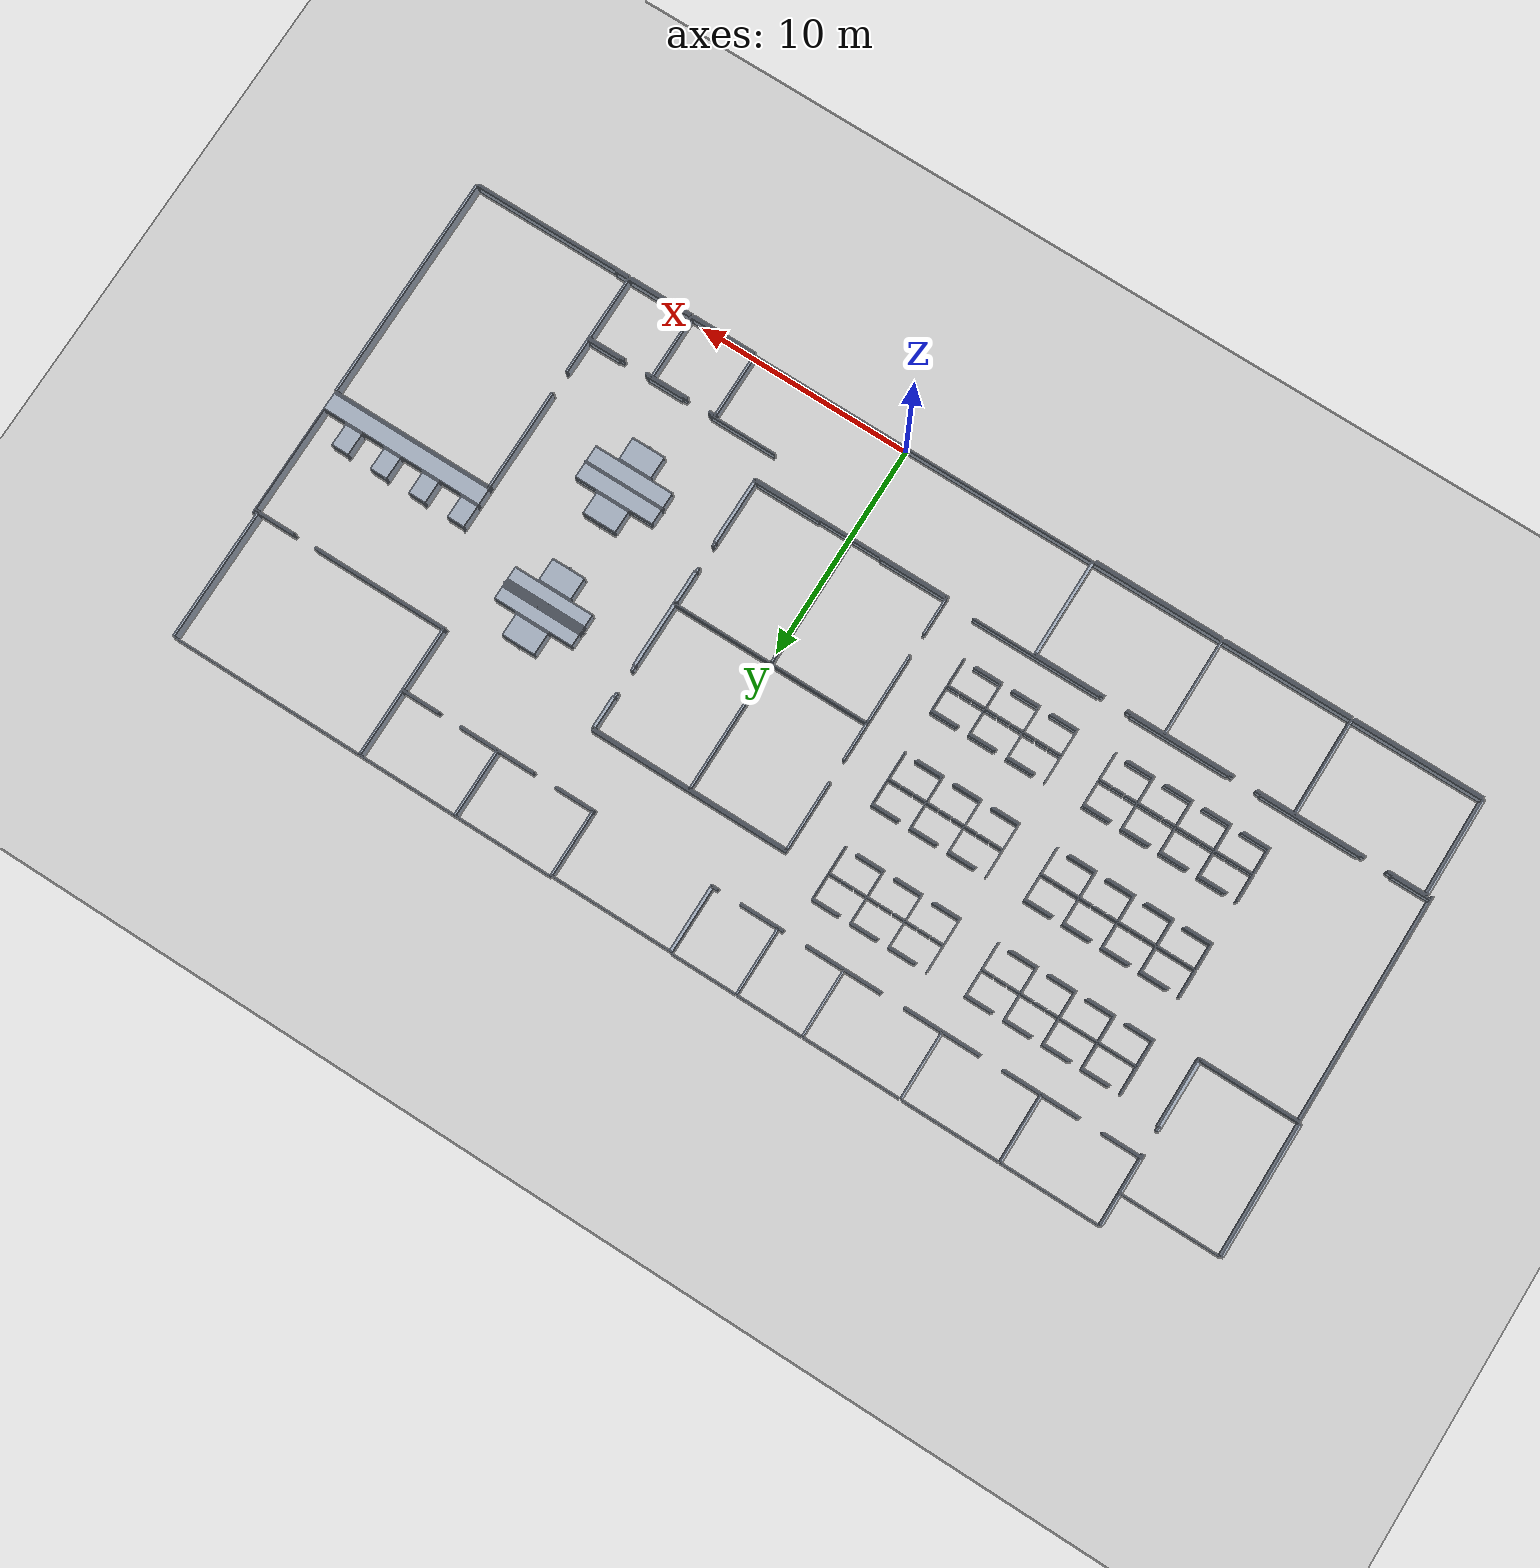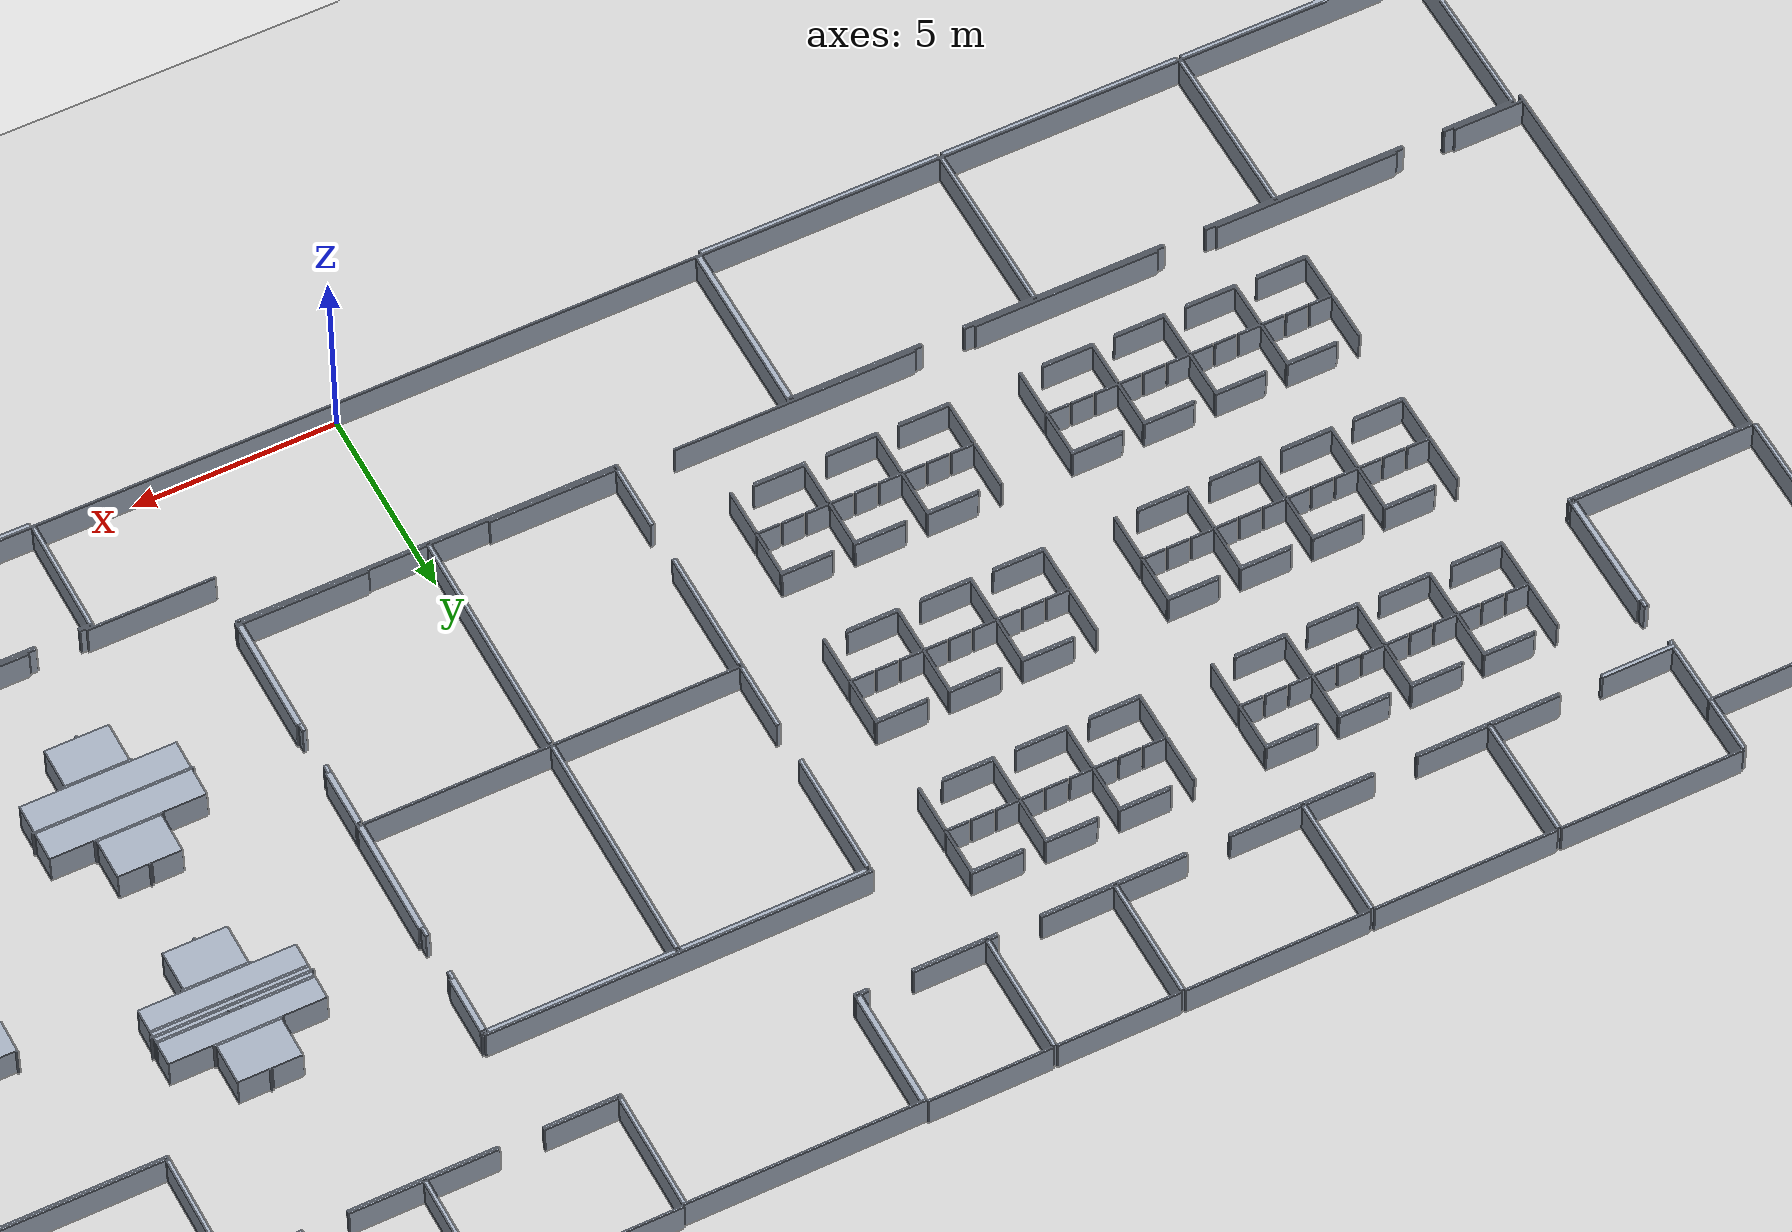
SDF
<?xml version="1.0" ?>
<sdf version="1.6">
  <world name="default">
    <gui>
      <camera name="user_camera">
        <pose>0 -18 30 0 0.9 1.5708</pose>
      </camera>
    </gui>
    <scene>
      <ambient>0.65 0.65 0.65 1</ambient>
      <background>0.55 0.58 0.62 1</background>
      <shadows>1</shadows>
      <grid>0</grid>
      <origin_visual>0</origin_visual>
    </scene>
    <include><uri>model://ground_plane</uri></include>
    <include><uri>model://sun</uri></include>
    <model name="slam_office_obstacles">
      <static>true</static>
      <link name="wall_0">
        <pose>-20.7000 22.5750 0.4 0 0 0</pose>
        <collision name="collision">
          <geometry><box><size>4.5000 0.0500 0.8</size></box></geometry>
        </collision>
        <visual name="visual">
          <geometry><box><size>4.5000 0.0500 0.8</size></box></geometry>
          <material>
            <ambient>0.62 0.66 0.72 1</ambient>
            <diffuse>0.62 0.66 0.72 1</diffuse>
          </material>
        </visual>
      </link>
      <link name="wall_1">
        <pose>-16.1000 22.5750 0.4 0 0 0</pose>
        <collision name="collision">
          <geometry><box><size>4.5000 0.0500 0.8</size></box></geometry>
        </collision>
        <visual name="visual">
          <geometry><box><size>4.5000 0.0500 0.8</size></box></geometry>
          <material>
            <ambient>0.62 0.66 0.72 1</ambient>
            <diffuse>0.62 0.66 0.72 1</diffuse>
          </material>
        </visual>
      </link>
      <link name="wall_2">
        <pose>-11.5000 22.5750 0.4 0 0 0</pose>
        <collision name="collision">
          <geometry><box><size>4.5000 0.0500 0.8</size></box></geometry>
        </collision>
        <visual name="visual">
          <geometry><box><size>4.5000 0.0500 0.8</size></box></geometry>
          <material>
            <ambient>0.62 0.66 0.72 1</ambient>
            <diffuse>0.62 0.66 0.72 1</diffuse>
          </material>
        </visual>
      </link>
      <link name="wall_3">
        <pose>-7.6500 22.5750 0.4 0 0 0</pose>
        <collision name="collision">
          <geometry><box><size>3.0000 0.0500 0.8</size></box></geometry>
        </collision>
        <visual name="visual">
          <geometry><box><size>3.0000 0.0500 0.8</size></box></geometry>
          <material>
            <ambient>0.62 0.66 0.72 1</ambient>
            <diffuse>0.62 0.66 0.72 1</diffuse>
          </material>
        </visual>
      </link>
      <link name="wall_4">
        <pose>-4.5500 22.5750 0.4 0 0 0</pose>
        <collision name="collision">
          <geometry><box><size>3.0000 0.0500 0.8</size></box></geometry>
        </collision>
        <visual name="visual">
          <geometry><box><size>3.0000 0.0500 0.8</size></box></geometry>
          <material>
            <ambient>0.62 0.66 0.72 1</ambient>
            <diffuse>0.62 0.66 0.72 1</diffuse>
          </material>
        </visual>
      </link>
      <link name="wall_5">
        <pose>5.0000 22.5750 0.4 0 0 0</pose>
        <collision name="collision">
          <geometry><box><size>4.5000 0.0500 0.8</size></box></geometry>
        </collision>
        <visual name="visual">
          <geometry><box><size>4.5000 0.0500 0.8</size></box></geometry>
          <material>
            <ambient>0.62 0.66 0.72 1</ambient>
            <diffuse>0.62 0.66 0.72 1</diffuse>
          </material>
        </visual>
      </link>
      <link name="wall_6">
        <pose>9.6000 22.5750 0.4 0 0 0</pose>
        <collision name="collision">
          <geometry><box><size>4.5000 0.0500 0.8</size></box></geometry>
        </collision>
        <visual name="visual">
          <geometry><box><size>4.5000 0.0500 0.8</size></box></geometry>
          <material>
            <ambient>0.62 0.66 0.72 1</ambient>
            <diffuse>0.62 0.66 0.72 1</diffuse>
          </material>
        </visual>
      </link>
      <link name="wall_7">
        <pose>16.4500 22.5750 0.4 0 0 0</pose>
        <collision name="collision">
          <geometry><box><size>9.0000 0.0500 0.8</size></box></geometry>
        </collision>
        <visual name="visual">
          <geometry><box><size>9.0000 0.0500 0.8</size></box></geometry>
          <material>
            <ambient>0.62 0.66 0.72 1</ambient>
            <diffuse>0.62 0.66 0.72 1</diffuse>
          </material>
        </visual>
      </link>
      <link name="wall_8">
        <pose>-0.1500 22.5250 0.4 0 0 0</pose>
        <collision name="collision">
          <geometry><box><size>5.8000 0.0500 0.8</size></box></geometry>
        </collision>
        <visual name="visual">
          <geometry><box><size>5.8000 0.0500 0.8</size></box></geometry>
          <material>
            <ambient>0.62 0.66 0.72 1</ambient>
            <diffuse>0.62 0.66 0.72 1</diffuse>
          </material>
        </visual>
      </link>
      <link name="wall_9">
        <pose>-23.0000 21.8250 0.4 0 0 0</pose>
        <collision name="collision">
          <geometry><box><size>0.1000 1.4500 0.8</size></box></geometry>
        </collision>
        <visual name="visual">
          <geometry><box><size>0.1000 1.4500 0.8</size></box></geometry>
          <material>
            <ambient>0.62 0.66 0.72 1</ambient>
            <diffuse>0.62 0.66 0.72 1</diffuse>
          </material>
        </visual>
      </link>
      <link name="wall_10">
        <pose>-25.2500 21.0750 0.4 0 0 0</pose>
        <collision name="collision">
          <geometry><box><size>4.6000 0.0500 0.8</size></box></geometry>
        </collision>
        <visual name="visual">
          <geometry><box><size>4.6000 0.0500 0.8</size></box></geometry>
          <material>
            <ambient>0.62 0.66 0.72 1</ambient>
            <diffuse>0.62 0.66 0.72 1</diffuse>
          </material>
        </visual>
      </link>
      <link name="wall_11">
        <pose>-18.4000 21.0250 0.4 0 0 0</pose>
        <collision name="collision">
          <geometry><box><size>0.1000 3.0500 0.8</size></box></geometry>
        </collision>
        <visual name="visual">
          <geometry><box><size>0.1000 3.0500 0.8</size></box></geometry>
          <material>
            <ambient>0.62 0.66 0.72 1</ambient>
            <diffuse>0.62 0.66 0.72 1</diffuse>
          </material>
        </visual>
      </link>
      <link name="wall_12">
        <pose>-13.8000 21.0250 0.4 0 0 0</pose>
        <collision name="collision">
          <geometry><box><size>0.1000 3.0500 0.8</size></box></geometry>
        </collision>
        <visual name="visual">
          <geometry><box><size>0.1000 3.0500 0.8</size></box></geometry>
          <material>
            <ambient>0.62 0.66 0.72 1</ambient>
            <diffuse>0.62 0.66 0.72 1</diffuse>
          </material>
        </visual>
      </link>
      <link name="wall_13">
        <pose>-9.2000 21.0250 0.4 0 0 0</pose>
        <collision name="collision">
          <geometry><box><size>0.1000 3.0500 0.8</size></box></geometry>
        </collision>
        <visual name="visual">
          <geometry><box><size>0.1000 3.0500 0.8</size></box></geometry>
          <material>
            <ambient>0.62 0.66 0.72 1</ambient>
            <diffuse>0.62 0.66 0.72 1</diffuse>
          </material>
        </visual>
      </link>
      <link name="wall_14">
        <pose>-6.1000 21.0250 0.4 0 0 0</pose>
        <collision name="collision">
          <geometry><box><size>0.1000 3.0500 0.8</size></box></geometry>
        </collision>
        <visual name="visual">
          <geometry><box><size>0.1000 3.0500 0.8</size></box></geometry>
          <material>
            <ambient>0.62 0.66 0.72 1</ambient>
            <diffuse>0.62 0.66 0.72 1</diffuse>
          </material>
        </visual>
      </link>
      <link name="wall_15">
        <pose>7.3000 21.0250 0.4 0 0 0</pose>
        <collision name="collision">
          <geometry><box><size>0.1000 3.0500 0.8</size></box></geometry>
        </collision>
        <visual name="visual">
          <geometry><box><size>0.1000 3.0500 0.8</size></box></geometry>
          <material>
            <ambient>0.62 0.66 0.72 1</ambient>
            <diffuse>0.62 0.66 0.72 1</diffuse>
          </material>
        </visual>
      </link>
      <link name="wall_16">
        <pose>11.9000 21.0250 0.4 0 0 0</pose>
        <collision name="collision">
          <geometry><box><size>0.1000 3.0500 0.8</size></box></geometry>
        </collision>
        <visual name="visual">
          <geometry><box><size>0.1000 3.0500 0.8</size></box></geometry>
          <material>
            <ambient>0.62 0.66 0.72 1</ambient>
            <diffuse>0.62 0.66 0.72 1</diffuse>
          </material>
        </visual>
      </link>
      <link name="wall_17">
        <pose>-2.9750 21.0000 0.4 0 0 0</pose>
        <collision name="collision">
          <geometry><box><size>0.1500 3.0000 0.8</size></box></geometry>
        </collision>
        <visual name="visual">
          <geometry><box><size>0.1500 3.0000 0.8</size></box></geometry>
          <material>
            <ambient>0.62 0.66 0.72 1</ambient>
            <diffuse>0.62 0.66 0.72 1</diffuse>
          </material>
        </visual>
      </link>
      <link name="wall_18">
        <pose>2.7000 21.0000 0.4 0 0 0</pose>
        <collision name="collision">
          <geometry><box><size>0.1000 3.0000 0.8</size></box></geometry>
        </collision>
        <visual name="visual">
          <geometry><box><size>0.1000 3.0000 0.8</size></box></geometry>
          <material>
            <ambient>0.62 0.66 0.72 1</ambient>
            <diffuse>0.62 0.66 0.72 1</diffuse>
          </material>
        </visual>
      </link>
      <link name="wall_19">
        <pose>-23.0000 20.2750 0.4 0 0 0</pose>
        <collision name="collision">
          <geometry><box><size>0.1000 1.5500 0.8</size></box></geometry>
        </collision>
        <visual name="visual">
          <geometry><box><size>0.1000 1.5500 0.8</size></box></geometry>
          <material>
            <ambient>0.62 0.66 0.72 1</ambient>
            <diffuse>0.62 0.66 0.72 1</diffuse>
          </material>
        </visual>
      </link>
      <link name="wall_20">
        <pose>-19.3000 19.4750 0.4 0 0 0</pose>
        <collision name="collision">
          <geometry><box><size>1.7000 0.0500 0.8</size></box></geometry>
        </collision>
        <visual name="visual">
          <geometry><box><size>1.7000 0.0500 0.8</size></box></geometry>
          <material>
            <ambient>0.62 0.66 0.72 1</ambient>
            <diffuse>0.62 0.66 0.72 1</diffuse>
          </material>
        </visual>
      </link>
      <link name="wall_21">
        <pose>-17.4750 19.4750 0.4 0 0 0</pose>
        <collision name="collision">
          <geometry><box><size>1.7500 0.0500 0.8</size></box></geometry>
        </collision>
        <visual name="visual">
          <geometry><box><size>1.7500 0.0500 0.8</size></box></geometry>
          <material>
            <ambient>0.62 0.66 0.72 1</ambient>
            <diffuse>0.62 0.66 0.72 1</diffuse>
          </material>
        </visual>
      </link>
      <link name="wall_22">
        <pose>-14.7000 19.4750 0.4 0 0 0</pose>
        <collision name="collision">
          <geometry><box><size>1.7000 0.0500 0.8</size></box></geometry>
        </collision>
        <visual name="visual">
          <geometry><box><size>1.7000 0.0500 0.8</size></box></geometry>
          <material>
            <ambient>0.62 0.66 0.72 1</ambient>
            <diffuse>0.62 0.66 0.72 1</diffuse>
          </material>
        </visual>
      </link>
      <link name="wall_23">
        <pose>-12.8750 19.4750 0.4 0 0 0</pose>
        <collision name="collision">
          <geometry><box><size>1.7500 0.0500 0.8</size></box></geometry>
        </collision>
        <visual name="visual">
          <geometry><box><size>1.7500 0.0500 0.8</size></box></geometry>
          <material>
            <ambient>0.62 0.66 0.72 1</ambient>
            <diffuse>0.62 0.66 0.72 1</diffuse>
          </material>
        </visual>
      </link>
      <link name="wall_24">
        <pose>-10.1000 19.4750 0.4 0 0 0</pose>
        <collision name="collision">
          <geometry><box><size>1.7000 0.0500 0.8</size></box></geometry>
        </collision>
        <visual name="visual">
          <geometry><box><size>1.7000 0.0500 0.8</size></box></geometry>
          <material>
            <ambient>0.62 0.66 0.72 1</ambient>
            <diffuse>0.62 0.66 0.72 1</diffuse>
          </material>
        </visual>
      </link>
      <link name="wall_25">
        <pose>-8.2750 19.4750 0.4 0 0 0</pose>
        <collision name="collision">
          <geometry><box><size>1.7500 0.0500 0.8</size></box></geometry>
        </collision>
        <visual name="visual">
          <geometry><box><size>1.7500 0.0500 0.8</size></box></geometry>
          <material>
            <ambient>0.62 0.66 0.72 1</ambient>
            <diffuse>0.62 0.66 0.72 1</diffuse>
          </material>
        </visual>
      </link>
      <link name="wall_26">
        <pose>-6.2500 19.4750 0.4 0 0 0</pose>
        <collision name="collision">
          <geometry><box><size>0.2000 0.0500 0.8</size></box></geometry>
        </collision>
        <visual name="visual">
          <geometry><box><size>0.2000 0.0500 0.8</size></box></geometry>
          <material>
            <ambient>0.62 0.66 0.72 1</ambient>
            <diffuse>0.62 0.66 0.72 1</diffuse>
          </material>
        </visual>
      </link>
      <link name="wall_27">
        <pose>-5.1750 19.4750 0.4 0 0 0</pose>
        <collision name="collision">
          <geometry><box><size>1.7500 0.0500 0.8</size></box></geometry>
        </collision>
        <visual name="visual">
          <geometry><box><size>1.7500 0.0500 0.8</size></box></geometry>
          <material>
            <ambient>0.62 0.66 0.72 1</ambient>
            <diffuse>0.62 0.66 0.72 1</diffuse>
          </material>
        </visual>
      </link>
      <link name="wall_28">
        <pose>-3.1500 19.4750 0.4 0 0 0</pose>
        <collision name="collision">
          <geometry><box><size>0.2000 0.0500 0.8</size></box></geometry>
        </collision>
        <visual name="visual">
          <geometry><box><size>0.2000 0.0500 0.8</size></box></geometry>
          <material>
            <ambient>0.62 0.66 0.72 1</ambient>
            <diffuse>0.62 0.66 0.72 1</diffuse>
          </material>
        </visual>
      </link>
      <link name="wall_29">
        <pose>-2.9250 19.4750 0.4 0 0 0</pose>
        <collision name="collision">
          <geometry><box><size>0.0500 0.0500 0.8</size></box></geometry>
        </collision>
        <visual name="visual">
          <geometry><box><size>0.0500 0.0500 0.8</size></box></geometry>
          <material>
            <ambient>0.62 0.66 0.72 1</ambient>
            <diffuse>0.62 0.66 0.72 1</diffuse>
          </material>
        </visual>
      </link>
      <link name="wall_30">
        <pose>2.6750 19.4750 0.4 0 0 0</pose>
        <collision name="collision">
          <geometry><box><size>0.0500 0.0500 0.8</size></box></geometry>
        </collision>
        <visual name="visual">
          <geometry><box><size>0.0500 0.0500 0.8</size></box></geometry>
          <material>
            <ambient>0.62 0.66 0.72 1</ambient>
            <diffuse>0.62 0.66 0.72 1</diffuse>
          </material>
        </visual>
      </link>
      <link name="wall_31">
        <pose>3.6250 19.4750 0.4 0 0 0</pose>
        <collision name="collision">
          <geometry><box><size>1.7500 0.0500 0.8</size></box></geometry>
        </collision>
        <visual name="visual">
          <geometry><box><size>1.7500 0.0500 0.8</size></box></geometry>
          <material>
            <ambient>0.62 0.66 0.72 1</ambient>
            <diffuse>0.62 0.66 0.72 1</diffuse>
          </material>
        </visual>
      </link>
      <link name="wall_32">
        <pose>6.4000 19.4750 0.4 0 0 0</pose>
        <collision name="collision">
          <geometry><box><size>1.7000 0.0500 0.8</size></box></geometry>
        </collision>
        <visual name="visual">
          <geometry><box><size>1.7000 0.0500 0.8</size></box></geometry>
          <material>
            <ambient>0.62 0.66 0.72 1</ambient>
            <diffuse>0.62 0.66 0.72 1</diffuse>
          </material>
        </visual>
      </link>
      <link name="wall_33">
        <pose>8.2250 19.4750 0.4 0 0 0</pose>
        <collision name="collision">
          <geometry><box><size>1.7500 0.0500 0.8</size></box></geometry>
        </collision>
        <visual name="visual">
          <geometry><box><size>1.7500 0.0500 0.8</size></box></geometry>
          <material>
            <ambient>0.62 0.66 0.72 1</ambient>
            <diffuse>0.62 0.66 0.72 1</diffuse>
          </material>
        </visual>
      </link>
      <link name="wall_34">
        <pose>-22.1250 19.4500 0.4 0 0 0</pose>
        <collision name="collision">
          <geometry><box><size>1.8500 0.1000 0.8</size></box></geometry>
        </collision>
        <visual name="visual">
          <geometry><box><size>1.8500 0.1000 0.8</size></box></geometry>
          <material>
            <ambient>0.62 0.66 0.72 1</ambient>
            <diffuse>0.62 0.66 0.72 1</diffuse>
          </material>
        </visual>
      </link>
      <link name="wall_35">
        <pose>11.0500 19.4500 0.4 0 0 0</pose>
        <collision name="collision">
          <geometry><box><size>1.8000 0.1000 0.8</size></box></geometry>
        </collision>
        <visual name="visual">
          <geometry><box><size>1.8000 0.1000 0.8</size></box></geometry>
          <material>
            <ambient>0.62 0.66 0.72 1</ambient>
            <diffuse>0.62 0.66 0.72 1</diffuse>
          </material>
        </visual>
      </link>
      <link name="wall_36">
        <pose>-18.3750 19.4250 0.4 0 0 0</pose>
        <collision name="collision">
          <geometry><box><size>3.5500 0.0500 0.8</size></box></geometry>
        </collision>
        <visual name="visual">
          <geometry><box><size>3.5500 0.0500 0.8</size></box></geometry>
          <material>
            <ambient>0.62 0.66 0.72 1</ambient>
            <diffuse>0.62 0.66 0.72 1</diffuse>
          </material>
        </visual>
      </link>
      <link name="wall_37">
        <pose>-13.7750 19.4250 0.4 0 0 0</pose>
        <collision name="collision">
          <geometry><box><size>3.5500 0.0500 0.8</size></box></geometry>
        </collision>
        <visual name="visual">
          <geometry><box><size>3.5500 0.0500 0.8</size></box></geometry>
          <material>
            <ambient>0.62 0.66 0.72 1</ambient>
            <diffuse>0.62 0.66 0.72 1</diffuse>
          </material>
        </visual>
      </link>
      <link name="wall_38">
        <pose>-9.1750 19.4250 0.4 0 0 0</pose>
        <collision name="collision">
          <geometry><box><size>3.5500 0.0500 0.8</size></box></geometry>
        </collision>
        <visual name="visual">
          <geometry><box><size>3.5500 0.0500 0.8</size></box></geometry>
          <material>
            <ambient>0.62 0.66 0.72 1</ambient>
            <diffuse>0.62 0.66 0.72 1</diffuse>
          </material>
        </visual>
      </link>
      <link name="wall_39">
        <pose>-5.3250 19.4250 0.4 0 0 0</pose>
        <collision name="collision">
          <geometry><box><size>2.0500 0.0500 0.8</size></box></geometry>
        </collision>
        <visual name="visual">
          <geometry><box><size>2.0500 0.0500 0.8</size></box></geometry>
          <material>
            <ambient>0.62 0.66 0.72 1</ambient>
            <diffuse>0.62 0.66 0.72 1</diffuse>
          </material>
        </visual>
      </link>
      <link name="wall_40">
        <pose>-3.0750 19.4250 0.4 0 0 0</pose>
        <collision name="collision">
          <geometry><box><size>0.3500 0.0500 0.8</size></box></geometry>
        </collision>
        <visual name="visual">
          <geometry><box><size>0.3500 0.0500 0.8</size></box></geometry>
          <material>
            <ambient>0.62 0.66 0.72 1</ambient>
            <diffuse>0.62 0.66 0.72 1</diffuse>
          </material>
        </visual>
      </link>
      <link name="wall_41">
        <pose>3.5750 19.4250 0.4 0 0 0</pose>
        <collision name="collision">
          <geometry><box><size>1.8500 0.0500 0.8</size></box></geometry>
        </collision>
        <visual name="visual">
          <geometry><box><size>1.8500 0.0500 0.8</size></box></geometry>
          <material>
            <ambient>0.62 0.66 0.72 1</ambient>
            <diffuse>0.62 0.66 0.72 1</diffuse>
          </material>
        </visual>
      </link>
      <link name="wall_42">
        <pose>7.3250 19.4250 0.4 0 0 0</pose>
        <collision name="collision">
          <geometry><box><size>3.5500 0.0500 0.8</size></box></geometry>
        </collision>
        <visual name="visual">
          <geometry><box><size>3.5500 0.0500 0.8</size></box></geometry>
          <material>
            <ambient>0.62 0.66 0.72 1</ambient>
            <diffuse>0.62 0.66 0.72 1</diffuse>
          </material>
        </visual>
      </link>
      <link name="wall_43">
        <pose>-23.0000 19.3500 0.4 0 0 0</pose>
        <collision name="collision">
          <geometry><box><size>0.1000 0.1000 0.8</size></box></geometry>
        </collision>
        <visual name="visual">
          <geometry><box><size>0.1000 0.1000 0.8</size></box></geometry>
          <material>
            <ambient>0.62 0.66 0.72 1</ambient>
            <diffuse>0.62 0.66 0.72 1</diffuse>
          </material>
        </visual>
      </link>
      <link name="wall_44">
        <pose>-23.0000 18.1500 0.4 0 0 0</pose>
        <collision name="collision">
          <geometry><box><size>0.1000 0.2000 0.8</size></box></geometry>
        </collision>
        <visual name="visual">
          <geometry><box><size>0.1000 0.2000 0.8</size></box></geometry>
          <material>
            <ambient>0.62 0.66 0.72 1</ambient>
            <diffuse>0.62 0.66 0.72 1</diffuse>
          </material>
        </visual>
      </link>
      <link name="wall_45">
        <pose>-19.8250 17.7750 0.4 0 0 0</pose>
        <collision name="collision">
          <geometry><box><size>1.2500 0.0500 0.8</size></box></geometry>
        </collision>
        <visual name="visual">
          <geometry><box><size>1.2500 0.0500 0.8</size></box></geometry>
          <material>
            <ambient>0.62 0.66 0.72 1</ambient>
            <diffuse>0.62 0.66 0.72 1</diffuse>
          </material>
        </visual>
      </link>
      <link name="wall_46">
        <pose>-18.0250 17.7750 0.4 0 0 0</pose>
        <collision name="collision">
          <geometry><box><size>1.2500 0.0500 0.8</size></box></geometry>
        </collision>
        <visual name="visual">
          <geometry><box><size>1.2500 0.0500 0.8</size></box></geometry>
          <material>
            <ambient>0.62 0.66 0.72 1</ambient>
            <diffuse>0.62 0.66 0.72 1</diffuse>
          </material>
        </visual>
      </link>
      <link name="wall_47">
        <pose>-16.2250 17.7750 0.4 0 0 0</pose>
        <collision name="collision">
          <geometry><box><size>1.2500 0.0500 0.8</size></box></geometry>
        </collision>
        <visual name="visual">
          <geometry><box><size>1.2500 0.0500 0.8</size></box></geometry>
          <material>
            <ambient>0.62 0.66 0.72 1</ambient>
            <diffuse>0.62 0.66 0.72 1</diffuse>
          </material>
        </visual>
      </link>
      <link name="wall_48">
        <pose>-14.4250 17.7750 0.4 0 0 0</pose>
        <collision name="collision">
          <geometry><box><size>1.2500 0.0500 0.8</size></box></geometry>
        </collision>
        <visual name="visual">
          <geometry><box><size>1.2500 0.0500 0.8</size></box></geometry>
          <material>
            <ambient>0.62 0.66 0.72 1</ambient>
            <diffuse>0.62 0.66 0.72 1</diffuse>
          </material>
        </visual>
      </link>
      <link name="wall_49">
        <pose>-10.8250 17.7750 0.4 0 0 0</pose>
        <collision name="collision">
          <geometry><box><size>1.2500 0.0500 0.8</size></box></geometry>
        </collision>
        <visual name="visual">
          <geometry><box><size>1.2500 0.0500 0.8</size></box></geometry>
          <material>
            <ambient>0.62 0.66 0.72 1</ambient>
            <diffuse>0.62 0.66 0.72 1</diffuse>
          </material>
        </visual>
      </link>
      <link name="wall_50">
        <pose>-9.0250 17.7750 0.4 0 0 0</pose>
        <collision name="collision">
          <geometry><box><size>1.2500 0.0500 0.8</size></box></geometry>
        </collision>
        <visual name="visual">
          <geometry><box><size>1.2500 0.0500 0.8</size></box></geometry>
          <material>
            <ambient>0.62 0.66 0.72 1</ambient>
            <diffuse>0.62 0.66 0.72 1</diffuse>
          </material>
        </visual>
      </link>
      <link name="wall_51">
        <pose>-7.2250 17.7750 0.4 0 0 0</pose>
        <collision name="collision">
          <geometry><box><size>1.2500 0.0500 0.8</size></box></geometry>
        </collision>
        <visual name="visual">
          <geometry><box><size>1.2500 0.0500 0.8</size></box></geometry>
          <material>
            <ambient>0.62 0.66 0.72 1</ambient>
            <diffuse>0.62 0.66 0.72 1</diffuse>
          </material>
        </visual>
      </link>
      <link name="wall_52">
        <pose>-19.8500 17.7250 0.4 0 0 0</pose>
        <collision name="collision">
          <geometry><box><size>1.3000 0.0500 0.8</size></box></geometry>
        </collision>
        <visual name="visual">
          <geometry><box><size>1.3000 0.0500 0.8</size></box></geometry>
          <material>
            <ambient>0.62 0.66 0.72 1</ambient>
            <diffuse>0.62 0.66 0.72 1</diffuse>
          </material>
        </visual>
      </link>
      <link name="wall_53">
        <pose>-18.0500 17.7250 0.4 0 0 0</pose>
        <collision name="collision">
          <geometry><box><size>1.3000 0.0500 0.8</size></box></geometry>
        </collision>
        <visual name="visual">
          <geometry><box><size>1.3000 0.0500 0.8</size></box></geometry>
          <material>
            <ambient>0.62 0.66 0.72 1</ambient>
            <diffuse>0.62 0.66 0.72 1</diffuse>
          </material>
        </visual>
      </link>
      <link name="wall_54">
        <pose>-16.2500 17.7250 0.4 0 0 0</pose>
        <collision name="collision">
          <geometry><box><size>1.3000 0.0500 0.8</size></box></geometry>
        </collision>
        <visual name="visual">
          <geometry><box><size>1.3000 0.0500 0.8</size></box></geometry>
          <material>
            <ambient>0.62 0.66 0.72 1</ambient>
            <diffuse>0.62 0.66 0.72 1</diffuse>
          </material>
        </visual>
      </link>
      <link name="wall_55">
        <pose>-14.4500 17.7250 0.4 0 0 0</pose>
        <collision name="collision">
          <geometry><box><size>1.3000 0.0500 0.8</size></box></geometry>
        </collision>
        <visual name="visual">
          <geometry><box><size>1.3000 0.0500 0.8</size></box></geometry>
          <material>
            <ambient>0.62 0.66 0.72 1</ambient>
            <diffuse>0.62 0.66 0.72 1</diffuse>
          </material>
        </visual>
      </link>
      <link name="wall_56">
        <pose>-10.8500 17.7250 0.4 0 0 0</pose>
        <collision name="collision">
          <geometry><box><size>1.3000 0.0500 0.8</size></box></geometry>
        </collision>
        <visual name="visual">
          <geometry><box><size>1.3000 0.0500 0.8</size></box></geometry>
          <material>
            <ambient>0.62 0.66 0.72 1</ambient>
            <diffuse>0.62 0.66 0.72 1</diffuse>
          </material>
        </visual>
      </link>
      <link name="wall_57">
        <pose>-9.0500 17.7250 0.4 0 0 0</pose>
        <collision name="collision">
          <geometry><box><size>1.3000 0.0500 0.8</size></box></geometry>
        </collision>
        <visual name="visual">
          <geometry><box><size>1.3000 0.0500 0.8</size></box></geometry>
          <material>
            <ambient>0.62 0.66 0.72 1</ambient>
            <diffuse>0.62 0.66 0.72 1</diffuse>
          </material>
        </visual>
      </link>
      <link name="wall_58">
        <pose>-7.2500 17.7250 0.4 0 0 0</pose>
        <collision name="collision">
          <geometry><box><size>1.3000 0.0500 0.8</size></box></geometry>
        </collision>
        <visual name="visual">
          <geometry><box><size>1.3000 0.0500 0.8</size></box></geometry>
          <material>
            <ambient>0.62 0.66 0.72 1</ambient>
            <diffuse>0.62 0.66 0.72 1</diffuse>
          </material>
        </visual>
      </link>
      <link name="wall_59">
        <pose>-0.1000 16.7250 0.4 0 0 0</pose>
        <collision name="collision">
          <geometry><box><size>9.3000 0.0500 0.8</size></box></geometry>
        </collision>
        <visual name="visual">
          <geometry><box><size>9.3000 0.0500 0.8</size></box></geometry>
          <material>
            <ambient>0.62 0.66 0.72 1</ambient>
            <diffuse>0.62 0.66 0.72 1</diffuse>
          </material>
        </visual>
      </link>
      <link name="wall_60">
        <pose>-4.7250 16.6750 0.4 0 0 0</pose>
        <collision name="collision">
          <geometry><box><size>0.0500 0.0500 0.8</size></box></geometry>
        </collision>
        <visual name="visual">
          <geometry><box><size>0.0500 0.0500 0.8</size></box></geometry>
          <material>
            <ambient>0.62 0.66 0.72 1</ambient>
            <diffuse>0.62 0.66 0.72 1</diffuse>
          </material>
        </visual>
      </link>
      <link name="wall_61">
        <pose>4.5750 16.6750 0.4 0 0 0</pose>
        <collision name="collision">
          <geometry><box><size>0.0500 0.0500 0.8</size></box></geometry>
        </collision>
        <visual name="visual">
          <geometry><box><size>0.0500 0.0500 0.8</size></box></geometry>
          <material>
            <ambient>0.62 0.66 0.72 1</ambient>
            <diffuse>0.62 0.66 0.72 1</diffuse>
          </material>
        </visual>
      </link>
      <link name="wall_62">
        <pose>-2.4000 16.6500 0.4 0 0 0</pose>
        <collision name="collision">
          <geometry><box><size>4.5000 0.1000 0.8</size></box></geometry>
        </collision>
        <visual name="visual">
          <geometry><box><size>4.5000 0.1000 0.8</size></box></geometry>
          <material>
            <ambient>0.62 0.66 0.72 1</ambient>
            <diffuse>0.62 0.66 0.72 1</diffuse>
          </material>
        </visual>
      </link>
      <link name="wall_63">
        <pose>2.2000 16.6500 0.4 0 0 0</pose>
        <collision name="collision">
          <geometry><box><size>4.5000 0.1000 0.8</size></box></geometry>
        </collision>
        <visual name="visual">
          <geometry><box><size>4.5000 0.1000 0.8</size></box></geometry>
          <material>
            <ambient>0.62 0.66 0.72 1</ambient>
            <diffuse>0.62 0.66 0.72 1</diffuse>
          </material>
        </visual>
      </link>
      <link name="wall_64">
        <pose>-21.0250 17.1750 0.4 0 0 0</pose>
        <collision name="collision">
          <geometry><box><size>0.0500 1.2500 0.8</size></box></geometry>
        </collision>
        <visual name="visual">
          <geometry><box><size>0.0500 1.2500 0.8</size></box></geometry>
          <material>
            <ambient>0.62 0.66 0.72 1</ambient>
            <diffuse>0.62 0.66 0.72 1</diffuse>
          </material>
        </visual>
      </link>
      <link name="wall_65">
        <pose>-12.0250 17.1750 0.4 0 0 0</pose>
        <collision name="collision">
          <geometry><box><size>0.0500 1.2500 0.8</size></box></geometry>
        </collision>
        <visual name="visual">
          <geometry><box><size>0.0500 1.2500 0.8</size></box></geometry>
          <material>
            <ambient>0.62 0.66 0.72 1</ambient>
            <diffuse>0.62 0.66 0.72 1</diffuse>
          </material>
        </visual>
      </link>
      <link name="wall_66">
        <pose>-19.2250 17.1250 0.4 0 0 0</pose>
        <collision name="collision">
          <geometry><box><size>0.0500 1.1500 0.8</size></box></geometry>
        </collision>
        <visual name="visual">
          <geometry><box><size>0.0500 1.1500 0.8</size></box></geometry>
          <material>
            <ambient>0.62 0.66 0.72 1</ambient>
            <diffuse>0.62 0.66 0.72 1</diffuse>
          </material>
        </visual>
      </link>
      <link name="wall_67">
        <pose>-17.4250 17.1250 0.4 0 0 0</pose>
        <collision name="collision">
          <geometry><box><size>0.0500 1.1500 0.8</size></box></geometry>
        </collision>
        <visual name="visual">
          <geometry><box><size>0.0500 1.1500 0.8</size></box></geometry>
          <material>
            <ambient>0.62 0.66 0.72 1</ambient>
            <diffuse>0.62 0.66 0.72 1</diffuse>
          </material>
        </visual>
      </link>
      <link name="wall_68">
        <pose>-15.6250 17.1250 0.4 0 0 0</pose>
        <collision name="collision">
          <geometry><box><size>0.0500 1.1500 0.8</size></box></geometry>
        </collision>
        <visual name="visual">
          <geometry><box><size>0.0500 1.1500 0.8</size></box></geometry>
          <material>
            <ambient>0.62 0.66 0.72 1</ambient>
            <diffuse>0.62 0.66 0.72 1</diffuse>
          </material>
        </visual>
      </link>
      <link name="wall_69">
        <pose>-13.8250 17.1250 0.4 0 0 0</pose>
        <collision name="collision">
          <geometry><box><size>0.0500 1.1500 0.8</size></box></geometry>
        </collision>
        <visual name="visual">
          <geometry><box><size>0.0500 1.1500 0.8</size></box></geometry>
          <material>
            <ambient>0.62 0.66 0.72 1</ambient>
            <diffuse>0.62 0.66 0.72 1</diffuse>
          </material>
        </visual>
      </link>
      <link name="wall_70">
        <pose>-10.2250 17.1250 0.4 0 0 0</pose>
        <collision name="collision">
          <geometry><box><size>0.0500 1.1500 0.8</size></box></geometry>
        </collision>
        <visual name="visual">
          <geometry><box><size>0.0500 1.1500 0.8</size></box></geometry>
          <material>
            <ambient>0.62 0.66 0.72 1</ambient>
            <diffuse>0.62 0.66 0.72 1</diffuse>
          </material>
        </visual>
      </link>
      <link name="wall_71">
        <pose>-8.4250 17.1250 0.4 0 0 0</pose>
        <collision name="collision">
          <geometry><box><size>0.0500 1.1500 0.8</size></box></geometry>
        </collision>
        <visual name="visual">
          <geometry><box><size>0.0500 1.1500 0.8</size></box></geometry>
          <material>
            <ambient>0.62 0.66 0.72 1</ambient>
            <diffuse>0.62 0.66 0.72 1</diffuse>
          </material>
        </visual>
      </link>
      <link name="wall_72">
        <pose>-6.6250 17.1250 0.4 0 0 0</pose>
        <collision name="collision">
          <geometry><box><size>0.0500 1.1500 0.8</size></box></geometry>
        </collision>
        <visual name="visual">
          <geometry><box><size>0.0500 1.1500 0.8</size></box></geometry>
          <material>
            <ambient>0.62 0.66 0.72 1</ambient>
            <diffuse>0.62 0.66 0.72 1</diffuse>
          </material>
        </visual>
      </link>
      <link name="wall_73">
        <pose>21.0000 19.5250 0.4 0 0 0</pose>
        <collision name="collision">
          <geometry><box><size>0.1000 6.0500 0.8</size></box></geometry>
        </collision>
        <visual name="visual">
          <geometry><box><size>0.1000 6.0500 0.8</size></box></geometry>
          <material>
            <ambient>0.62 0.66 0.72 1</ambient>
            <diffuse>0.62 0.66 0.72 1</diffuse>
          </material>
        </visual>
      </link>
      <link name="wall_74">
        <pose>11.9000 17.9500 0.4 0 0 0</pose>
        <collision name="collision">
          <geometry><box><size>0.1000 2.9000 0.8</size></box></geometry>
        </collision>
        <visual name="visual">
          <geometry><box><size>0.1000 2.9000 0.8</size></box></geometry>
          <material>
            <ambient>0.62 0.66 0.72 1</ambient>
            <diffuse>0.62 0.66 0.72 1</diffuse>
          </material>
        </visual>
      </link>
      <link name="wall_75">
        <pose>-20.7250 16.5250 0.4 0 0 0</pose>
        <collision name="collision">
          <geometry><box><size>0.5500 0.0500 0.8</size></box></geometry>
        </collision>
        <visual name="visual">
          <geometry><box><size>0.5500 0.0500 0.8</size></box></geometry>
          <material>
            <ambient>0.62 0.66 0.72 1</ambient>
            <diffuse>0.62 0.66 0.72 1</diffuse>
          </material>
        </visual>
      </link>
      <link name="wall_76">
        <pose>-20.1250 16.5250 0.4 0 0 0</pose>
        <collision name="collision">
          <geometry><box><size>0.5500 0.0500 0.8</size></box></geometry>
        </collision>
        <visual name="visual">
          <geometry><box><size>0.5500 0.0500 0.8</size></box></geometry>
          <material>
            <ambient>0.62 0.66 0.72 1</ambient>
            <diffuse>0.62 0.66 0.72 1</diffuse>
          </material>
        </visual>
      </link>
      <link name="wall_77">
        <pose>-19.5250 16.5250 0.4 0 0 0</pose>
        <collision name="collision">
          <geometry><box><size>0.5500 0.0500 0.8</size></box></geometry>
        </collision>
        <visual name="visual">
          <geometry><box><size>0.5500 0.0500 0.8</size></box></geometry>
          <material>
            <ambient>0.62 0.66 0.72 1</ambient>
            <diffuse>0.62 0.66 0.72 1</diffuse>
          </material>
        </visual>
      </link>
      <link name="wall_78">
        <pose>-18.9250 16.5250 0.4 0 0 0</pose>
        <collision name="collision">
          <geometry><box><size>0.5500 0.0500 0.8</size></box></geometry>
        </collision>
        <visual name="visual">
          <geometry><box><size>0.5500 0.0500 0.8</size></box></geometry>
          <material>
            <ambient>0.62 0.66 0.72 1</ambient>
            <diffuse>0.62 0.66 0.72 1</diffuse>
          </material>
        </visual>
      </link>
      <link name="wall_79">
        <pose>-18.3250 16.5250 0.4 0 0 0</pose>
        <collision name="collision">
          <geometry><box><size>0.5500 0.0500 0.8</size></box></geometry>
        </collision>
        <visual name="visual">
          <geometry><box><size>0.5500 0.0500 0.8</size></box></geometry>
          <material>
            <ambient>0.62 0.66 0.72 1</ambient>
            <diffuse>0.62 0.66 0.72 1</diffuse>
          </material>
        </visual>
      </link>
      <link name="wall_80">
        <pose>-17.7250 16.5250 0.4 0 0 0</pose>
        <collision name="collision">
          <geometry><box><size>0.5500 0.0500 0.8</size></box></geometry>
        </collision>
        <visual name="visual">
          <geometry><box><size>0.5500 0.0500 0.8</size></box></geometry>
          <material>
            <ambient>0.62 0.66 0.72 1</ambient>
            <diffuse>0.62 0.66 0.72 1</diffuse>
          </material>
        </visual>
      </link>
      <link name="wall_81">
        <pose>-17.1250 16.5250 0.4 0 0 0</pose>
        <collision name="collision">
          <geometry><box><size>0.5500 0.0500 0.8</size></box></geometry>
        </collision>
        <visual name="visual">
          <geometry><box><size>0.5500 0.0500 0.8</size></box></geometry>
          <material>
            <ambient>0.62 0.66 0.72 1</ambient>
            <diffuse>0.62 0.66 0.72 1</diffuse>
          </material>
        </visual>
      </link>
      <link name="wall_82">
        <pose>-16.5250 16.5250 0.4 0 0 0</pose>
        <collision name="collision">
          <geometry><box><size>0.5500 0.0500 0.8</size></box></geometry>
        </collision>
        <visual name="visual">
          <geometry><box><size>0.5500 0.0500 0.8</size></box></geometry>
          <material>
            <ambient>0.62 0.66 0.72 1</ambient>
            <diffuse>0.62 0.66 0.72 1</diffuse>
          </material>
        </visual>
      </link>
      <link name="wall_83">
        <pose>-15.9250 16.5250 0.4 0 0 0</pose>
        <collision name="collision">
          <geometry><box><size>0.5500 0.0500 0.8</size></box></geometry>
        </collision>
        <visual name="visual">
          <geometry><box><size>0.5500 0.0500 0.8</size></box></geometry>
          <material>
            <ambient>0.62 0.66 0.72 1</ambient>
            <diffuse>0.62 0.66 0.72 1</diffuse>
          </material>
        </visual>
      </link>
      <link name="wall_84">
        <pose>-15.3250 16.5250 0.4 0 0 0</pose>
        <collision name="collision">
          <geometry><box><size>0.5500 0.0500 0.8</size></box></geometry>
        </collision>
        <visual name="visual">
          <geometry><box><size>0.5500 0.0500 0.8</size></box></geometry>
          <material>
            <ambient>0.62 0.66 0.72 1</ambient>
            <diffuse>0.62 0.66 0.72 1</diffuse>
          </material>
        </visual>
      </link>
      <link name="wall_85">
        <pose>-14.7250 16.5250 0.4 0 0 0</pose>
        <collision name="collision">
          <geometry><box><size>0.5500 0.0500 0.8</size></box></geometry>
        </collision>
        <visual name="visual">
          <geometry><box><size>0.5500 0.0500 0.8</size></box></geometry>
          <material>
            <ambient>0.62 0.66 0.72 1</ambient>
            <diffuse>0.62 0.66 0.72 1</diffuse>
          </material>
        </visual>
      </link>
      <link name="wall_86">
        <pose>-14.1250 16.5250 0.4 0 0 0</pose>
        <collision name="collision">
          <geometry><box><size>0.5500 0.0500 0.8</size></box></geometry>
        </collision>
        <visual name="visual">
          <geometry><box><size>0.5500 0.0500 0.8</size></box></geometry>
          <material>
            <ambient>0.62 0.66 0.72 1</ambient>
            <diffuse>0.62 0.66 0.72 1</diffuse>
          </material>
        </visual>
      </link>
      <link name="wall_87">
        <pose>-11.7250 16.5250 0.4 0 0 0</pose>
        <collision name="collision">
          <geometry><box><size>0.5500 0.0500 0.8</size></box></geometry>
        </collision>
        <visual name="visual">
          <geometry><box><size>0.5500 0.0500 0.8</size></box></geometry>
          <material>
            <ambient>0.62 0.66 0.72 1</ambient>
            <diffuse>0.62 0.66 0.72 1</diffuse>
          </material>
        </visual>
      </link>
      <link name="wall_88">
        <pose>-11.1250 16.5250 0.4 0 0 0</pose>
        <collision name="collision">
          <geometry><box><size>0.5500 0.0500 0.8</size></box></geometry>
        </collision>
        <visual name="visual">
          <geometry><box><size>0.5500 0.0500 0.8</size></box></geometry>
          <material>
            <ambient>0.62 0.66 0.72 1</ambient>
            <diffuse>0.62 0.66 0.72 1</diffuse>
          </material>
        </visual>
      </link>
      <link name="wall_89">
        <pose>-10.5250 16.5250 0.4 0 0 0</pose>
        <collision name="collision">
          <geometry><box><size>0.5500 0.0500 0.8</size></box></geometry>
        </collision>
        <visual name="visual">
          <geometry><box><size>0.5500 0.0500 0.8</size></box></geometry>
          <material>
            <ambient>0.62 0.66 0.72 1</ambient>
            <diffuse>0.62 0.66 0.72 1</diffuse>
          </material>
        </visual>
      </link>
      <link name="wall_90">
        <pose>-9.9250 16.5250 0.4 0 0 0</pose>
        <collision name="collision">
          <geometry><box><size>0.5500 0.0500 0.8</size></box></geometry>
        </collision>
        <visual name="visual">
          <geometry><box><size>0.5500 0.0500 0.8</size></box></geometry>
          <material>
            <ambient>0.62 0.66 0.72 1</ambient>
            <diffuse>0.62 0.66 0.72 1</diffuse>
          </material>
        </visual>
      </link>
      <link name="wall_91">
        <pose>-9.3250 16.5250 0.4 0 0 0</pose>
        <collision name="collision">
          <geometry><box><size>0.5500 0.0500 0.8</size></box></geometry>
        </collision>
        <visual name="visual">
          <geometry><box><size>0.5500 0.0500 0.8</size></box></geometry>
          <material>
            <ambient>0.62 0.66 0.72 1</ambient>
            <diffuse>0.62 0.66 0.72 1</diffuse>
          </material>
        </visual>
      </link>
      <link name="wall_92">
        <pose>-8.7250 16.5250 0.4 0 0 0</pose>
        <collision name="collision">
          <geometry><box><size>0.5500 0.0500 0.8</size></box></geometry>
        </collision>
        <visual name="visual">
          <geometry><box><size>0.5500 0.0500 0.8</size></box></geometry>
          <material>
            <ambient>0.62 0.66 0.72 1</ambient>
            <diffuse>0.62 0.66 0.72 1</diffuse>
          </material>
        </visual>
      </link>
      <link name="wall_93">
        <pose>-8.1250 16.5250 0.4 0 0 0</pose>
        <collision name="collision">
          <geometry><box><size>0.5500 0.0500 0.8</size></box></geometry>
        </collision>
        <visual name="visual">
          <geometry><box><size>0.5500 0.0500 0.8</size></box></geometry>
          <material>
            <ambient>0.62 0.66 0.72 1</ambient>
            <diffuse>0.62 0.66 0.72 1</diffuse>
          </material>
        </visual>
      </link>
      <link name="wall_94">
        <pose>-7.5250 16.5250 0.4 0 0 0</pose>
        <collision name="collision">
          <geometry><box><size>0.5500 0.0500 0.8</size></box></geometry>
        </collision>
        <visual name="visual">
          <geometry><box><size>0.5500 0.0500 0.8</size></box></geometry>
          <material>
            <ambient>0.62 0.66 0.72 1</ambient>
            <diffuse>0.62 0.66 0.72 1</diffuse>
          </material>
        </visual>
      </link>
      <link name="wall_95">
        <pose>-6.9250 16.5250 0.4 0 0 0</pose>
        <collision name="collision">
          <geometry><box><size>0.5500 0.0500 0.8</size></box></geometry>
        </collision>
        <visual name="visual">
          <geometry><box><size>0.5500 0.0500 0.8</size></box></geometry>
          <material>
            <ambient>0.62 0.66 0.72 1</ambient>
            <diffuse>0.62 0.66 0.72 1</diffuse>
          </material>
        </visual>
      </link>
      <link name="wall_96">
        <pose>21.1750 16.5250 0.4 0 0 0</pose>
        <collision name="collision">
          <geometry><box><size>0.0500 0.1500 0.8</size></box></geometry>
        </collision>
        <visual name="visual">
          <geometry><box><size>0.0500 0.1500 0.8</size></box></geometry>
          <material>
            <ambient>0.62 0.66 0.72 1</ambient>
            <diffuse>0.62 0.66 0.72 1</diffuse>
          </material>
        </visual>
      </link>
      <link name="wall_97">
        <pose>11.8750 16.4750 0.4 0 0 0</pose>
        <collision name="collision">
          <geometry><box><size>0.0500 0.0500 0.8</size></box></geometry>
        </collision>
        <visual name="visual">
          <geometry><box><size>0.0500 0.0500 0.8</size></box></geometry>
          <material>
            <ambient>0.62 0.66 0.72 1</ambient>
            <diffuse>0.62 0.66 0.72 1</diffuse>
          </material>
        </visual>
      </link>
      <link name="wall_98">
        <pose>15.0750 16.4750 0.4 0 0 0</pose>
        <collision name="collision">
          <geometry><box><size>6.2500 0.0500 0.8</size></box></geometry>
        </collision>
        <visual name="visual">
          <geometry><box><size>6.2500 0.0500 0.8</size></box></geometry>
          <material>
            <ambient>0.62 0.66 0.72 1</ambient>
            <diffuse>0.62 0.66 0.72 1</diffuse>
          </material>
        </visual>
      </link>
      <link name="wall_99">
        <pose>20.1000 16.4750 0.4 0 0 0</pose>
        <collision name="collision">
          <geometry><box><size>1.7000 0.0500 0.8</size></box></geometry>
        </collision>
        <visual name="visual">
          <geometry><box><size>1.7000 0.0500 0.8</size></box></geometry>
          <material>
            <ambient>0.62 0.66 0.72 1</ambient>
            <diffuse>0.62 0.66 0.72 1</diffuse>
          </material>
        </visual>
      </link>
      <link name="wall_100">
        <pose>15.0250 16.4250 0.4 0 0 0</pose>
        <collision name="collision">
          <geometry><box><size>6.3500 0.0500 0.8</size></box></geometry>
        </collision>
        <visual name="visual">
          <geometry><box><size>6.3500 0.0500 0.8</size></box></geometry>
          <material>
            <ambient>0.62 0.66 0.72 1</ambient>
            <diffuse>0.62 0.66 0.72 1</diffuse>
          </material>
        </visual>
      </link>
      <link name="wall_101">
        <pose>20.2250 16.4250 0.4 0 0 0</pose>
        <collision name="collision">
          <geometry><box><size>1.9500 0.0500 0.8</size></box></geometry>
        </collision>
        <visual name="visual">
          <geometry><box><size>1.9500 0.0500 0.8</size></box></geometry>
          <material>
            <ambient>0.62 0.66 0.72 1</ambient>
            <diffuse>0.62 0.66 0.72 1</diffuse>
          </material>
        </visual>
      </link>
      <link name="wall_102">
        <pose>8.9750 15.4250 0.4 0 0 0</pose>
        <collision name="collision">
          <geometry><box><size>0.0500 0.0500 0.8</size></box></geometry>
        </collision>
        <visual name="visual">
          <geometry><box><size>0.0500 0.0500 0.8</size></box></geometry>
          <material>
            <ambient>0.62 0.66 0.72 1</ambient>
            <diffuse>0.62 0.66 0.72 1</diffuse>
          </material>
        </visual>
      </link>
      <link name="wall_103">
        <pose>-21.0250 15.9250 0.4 0 0 0</pose>
        <collision name="collision">
          <geometry><box><size>0.0500 1.1500 0.8</size></box></geometry>
        </collision>
        <visual name="visual">
          <geometry><box><size>0.0500 1.1500 0.8</size></box></geometry>
          <material>
            <ambient>0.62 0.66 0.72 1</ambient>
            <diffuse>0.62 0.66 0.72 1</diffuse>
          </material>
        </visual>
      </link>
      <link name="wall_104">
        <pose>-19.2250 15.9250 0.4 0 0 0</pose>
        <collision name="collision">
          <geometry><box><size>0.0500 1.1500 0.8</size></box></geometry>
        </collision>
        <visual name="visual">
          <geometry><box><size>0.0500 1.1500 0.8</size></box></geometry>
          <material>
            <ambient>0.62 0.66 0.72 1</ambient>
            <diffuse>0.62 0.66 0.72 1</diffuse>
          </material>
        </visual>
      </link>
      <link name="wall_105">
        <pose>-17.4250 15.9250 0.4 0 0 0</pose>
        <collision name="collision">
          <geometry><box><size>0.0500 1.1500 0.8</size></box></geometry>
        </collision>
        <visual name="visual">
          <geometry><box><size>0.0500 1.1500 0.8</size></box></geometry>
          <material>
            <ambient>0.62 0.66 0.72 1</ambient>
            <diffuse>0.62 0.66 0.72 1</diffuse>
          </material>
        </visual>
      </link>
      <link name="wall_106">
        <pose>-15.6250 15.9250 0.4 0 0 0</pose>
        <collision name="collision">
          <geometry><box><size>0.0500 1.1500 0.8</size></box></geometry>
        </collision>
        <visual name="visual">
          <geometry><box><size>0.0500 1.1500 0.8</size></box></geometry>
          <material>
            <ambient>0.62 0.66 0.72 1</ambient>
            <diffuse>0.62 0.66 0.72 1</diffuse>
          </material>
        </visual>
      </link>
      <link name="wall_107">
        <pose>-12.0250 15.9250 0.4 0 0 0</pose>
        <collision name="collision">
          <geometry><box><size>0.0500 1.1500 0.8</size></box></geometry>
        </collision>
        <visual name="visual">
          <geometry><box><size>0.0500 1.1500 0.8</size></box></geometry>
          <material>
            <ambient>0.62 0.66 0.72 1</ambient>
            <diffuse>0.62 0.66 0.72 1</diffuse>
          </material>
        </visual>
      </link>
      <link name="wall_108">
        <pose>-10.2250 15.9250 0.4 0 0 0</pose>
        <collision name="collision">
          <geometry><box><size>0.0500 1.1500 0.8</size></box></geometry>
        </collision>
        <visual name="visual">
          <geometry><box><size>0.0500 1.1500 0.8</size></box></geometry>
          <material>
            <ambient>0.62 0.66 0.72 1</ambient>
            <diffuse>0.62 0.66 0.72 1</diffuse>
          </material>
        </visual>
      </link>
      <link name="wall_109">
        <pose>-8.4250 15.9250 0.4 0 0 0</pose>
        <collision name="collision">
          <geometry><box><size>0.0500 1.1500 0.8</size></box></geometry>
        </collision>
        <visual name="visual">
          <geometry><box><size>0.0500 1.1500 0.8</size></box></geometry>
          <material>
            <ambient>0.62 0.66 0.72 1</ambient>
            <diffuse>0.62 0.66 0.72 1</diffuse>
          </material>
        </visual>
      </link>
      <link name="wall_110">
        <pose>-20.4000 15.3250 0.4 0 0 0</pose>
        <collision name="collision">
          <geometry><box><size>1.3000 0.0500 0.8</size></box></geometry>
        </collision>
        <visual name="visual">
          <geometry><box><size>1.3000 0.0500 0.8</size></box></geometry>
          <material>
            <ambient>0.62 0.66 0.72 1</ambient>
            <diffuse>0.62 0.66 0.72 1</diffuse>
          </material>
        </visual>
      </link>
      <link name="wall_111">
        <pose>-18.6000 15.3250 0.4 0 0 0</pose>
        <collision name="collision">
          <geometry><box><size>1.3000 0.0500 0.8</size></box></geometry>
        </collision>
        <visual name="visual">
          <geometry><box><size>1.3000 0.0500 0.8</size></box></geometry>
          <material>
            <ambient>0.62 0.66 0.72 1</ambient>
            <diffuse>0.62 0.66 0.72 1</diffuse>
          </material>
        </visual>
      </link>
      <link name="wall_112">
        <pose>-16.8000 15.3250 0.4 0 0 0</pose>
        <collision name="collision">
          <geometry><box><size>1.3000 0.0500 0.8</size></box></geometry>
        </collision>
        <visual name="visual">
          <geometry><box><size>1.3000 0.0500 0.8</size></box></geometry>
          <material>
            <ambient>0.62 0.66 0.72 1</ambient>
            <diffuse>0.62 0.66 0.72 1</diffuse>
          </material>
        </visual>
      </link>
      <link name="wall_113">
        <pose>-15.0000 15.3250 0.4 0 0 0</pose>
        <collision name="collision">
          <geometry><box><size>1.3000 0.0500 0.8</size></box></geometry>
        </collision>
        <visual name="visual">
          <geometry><box><size>1.3000 0.0500 0.8</size></box></geometry>
          <material>
            <ambient>0.62 0.66 0.72 1</ambient>
            <diffuse>0.62 0.66 0.72 1</diffuse>
          </material>
        </visual>
      </link>
      <link name="wall_114">
        <pose>-11.4000 15.3250 0.4 0 0 0</pose>
        <collision name="collision">
          <geometry><box><size>1.3000 0.0500 0.8</size></box></geometry>
        </collision>
        <visual name="visual">
          <geometry><box><size>1.3000 0.0500 0.8</size></box></geometry>
          <material>
            <ambient>0.62 0.66 0.72 1</ambient>
            <diffuse>0.62 0.66 0.72 1</diffuse>
          </material>
        </visual>
      </link>
      <link name="wall_115">
        <pose>-9.6000 15.3250 0.4 0 0 0</pose>
        <collision name="collision">
          <geometry><box><size>1.3000 0.0500 0.8</size></box></geometry>
        </collision>
        <visual name="visual">
          <geometry><box><size>1.3000 0.0500 0.8</size></box></geometry>
          <material>
            <ambient>0.62 0.66 0.72 1</ambient>
            <diffuse>0.62 0.66 0.72 1</diffuse>
          </material>
        </visual>
      </link>
      <link name="wall_116">
        <pose>-7.8000 15.3250 0.4 0 0 0</pose>
        <collision name="collision">
          <geometry><box><size>1.3000 0.0500 0.8</size></box></geometry>
        </collision>
        <visual name="visual">
          <geometry><box><size>1.3000 0.0500 0.8</size></box></geometry>
          <material>
            <ambient>0.62 0.66 0.72 1</ambient>
            <diffuse>0.62 0.66 0.72 1</diffuse>
          </material>
        </visual>
      </link>
      <link name="wall_117">
        <pose>-13.8250 15.8750 0.4 0 0 0</pose>
        <collision name="collision">
          <geometry><box><size>0.0500 1.2500 0.8</size></box></geometry>
        </collision>
        <visual name="visual">
          <geometry><box><size>0.0500 1.2500 0.8</size></box></geometry>
          <material>
            <ambient>0.62 0.66 0.72 1</ambient>
            <diffuse>0.62 0.66 0.72 1</diffuse>
          </material>
        </visual>
      </link>
      <link name="wall_118">
        <pose>-6.6250 15.8750 0.4 0 0 0</pose>
        <collision name="collision">
          <geometry><box><size>0.0500 1.2500 0.8</size></box></geometry>
        </collision>
        <visual name="visual">
          <geometry><box><size>0.0500 1.2500 0.8</size></box></geometry>
          <material>
            <ambient>0.62 0.66 0.72 1</ambient>
            <diffuse>0.62 0.66 0.72 1</diffuse>
          </material>
        </visual>
      </link>
      <link name="wall_119">
        <pose>-20.4250 15.2750 0.4 0 0 0</pose>
        <collision name="collision">
          <geometry><box><size>1.2500 0.0500 0.8</size></box></geometry>
        </collision>
        <visual name="visual">
          <geometry><box><size>1.2500 0.0500 0.8</size></box></geometry>
          <material>
            <ambient>0.62 0.66 0.72 1</ambient>
            <diffuse>0.62 0.66 0.72 1</diffuse>
          </material>
        </visual>
      </link>
      <link name="wall_120">
        <pose>-18.6250 15.2750 0.4 0 0 0</pose>
        <collision name="collision">
          <geometry><box><size>1.2500 0.0500 0.8</size></box></geometry>
        </collision>
        <visual name="visual">
          <geometry><box><size>1.2500 0.0500 0.8</size></box></geometry>
          <material>
            <ambient>0.62 0.66 0.72 1</ambient>
            <diffuse>0.62 0.66 0.72 1</diffuse>
          </material>
        </visual>
      </link>
      <link name="wall_121">
        <pose>-16.8250 15.2750 0.4 0 0 0</pose>
        <collision name="collision">
          <geometry><box><size>1.2500 0.0500 0.8</size></box></geometry>
        </collision>
        <visual name="visual">
          <geometry><box><size>1.2500 0.0500 0.8</size></box></geometry>
          <material>
            <ambient>0.62 0.66 0.72 1</ambient>
            <diffuse>0.62 0.66 0.72 1</diffuse>
          </material>
        </visual>
      </link>
      <link name="wall_122">
        <pose>-15.0250 15.2750 0.4 0 0 0</pose>
        <collision name="collision">
          <geometry><box><size>1.2500 0.0500 0.8</size></box></geometry>
        </collision>
        <visual name="visual">
          <geometry><box><size>1.2500 0.0500 0.8</size></box></geometry>
          <material>
            <ambient>0.62 0.66 0.72 1</ambient>
            <diffuse>0.62 0.66 0.72 1</diffuse>
          </material>
        </visual>
      </link>
      <link name="wall_123">
        <pose>-11.4250 15.2750 0.4 0 0 0</pose>
        <collision name="collision">
          <geometry><box><size>1.2500 0.0500 0.8</size></box></geometry>
        </collision>
        <visual name="visual">
          <geometry><box><size>1.2500 0.0500 0.8</size></box></geometry>
          <material>
            <ambient>0.62 0.66 0.72 1</ambient>
            <diffuse>0.62 0.66 0.72 1</diffuse>
          </material>
        </visual>
      </link>
      <link name="wall_124">
        <pose>-9.6250 15.2750 0.4 0 0 0</pose>
        <collision name="collision">
          <geometry><box><size>1.2500 0.0500 0.8</size></box></geometry>
        </collision>
        <visual name="visual">
          <geometry><box><size>1.2500 0.0500 0.8</size></box></geometry>
          <material>
            <ambient>0.62 0.66 0.72 1</ambient>
            <diffuse>0.62 0.66 0.72 1</diffuse>
          </material>
        </visual>
      </link>
      <link name="wall_125">
        <pose>-7.8250 15.2750 0.4 0 0 0</pose>
        <collision name="collision">
          <geometry><box><size>1.2500 0.0500 0.8</size></box></geometry>
        </collision>
        <visual name="visual">
          <geometry><box><size>1.2500 0.0500 0.8</size></box></geometry>
          <material>
            <ambient>0.62 0.66 0.72 1</ambient>
            <diffuse>0.62 0.66 0.72 1</diffuse>
          </material>
        </visual>
      </link>
      <link name="wall_126">
        <pose>4.5250 15.8500 0.4 0 0 0</pose>
        <collision name="collision">
          <geometry><box><size>0.1500 1.5000 0.8</size></box></geometry>
        </collision>
        <visual name="visual">
          <geometry><box><size>0.1500 1.5000 0.8</size></box></geometry>
          <material>
            <ambient>0.62 0.66 0.72 1</ambient>
            <diffuse>0.62 0.66 0.72 1</diffuse>
          </material>
        </visual>
      </link>
      <link name="wall_127">
        <pose>-22.9750 16.5500 0.4 0 0 0</pose>
        <collision name="collision">
          <geometry><box><size>0.1500 3.0000 0.8</size></box></geometry>
        </collision>
        <visual name="visual">
          <geometry><box><size>0.1500 3.0000 0.8</size></box></geometry>
          <material>
            <ambient>0.62 0.66 0.72 1</ambient>
            <diffuse>0.62 0.66 0.72 1</diffuse>
          </material>
        </visual>
      </link>
      <link name="wall_128">
        <pose>-27.6000 18.0250 0.4 0 0 0</pose>
        <collision name="collision">
          <geometry><box><size>0.1000 6.0500 0.8</size></box></geometry>
        </collision>
        <visual name="visual">
          <geometry><box><size>0.1000 6.0500 0.8</size></box></geometry>
          <material>
            <ambient>0.62 0.66 0.72 1</ambient>
            <diffuse>0.62 0.66 0.72 1</diffuse>
          </material>
        </visual>
      </link>
      <link name="wall_129">
        <pose>-22.9250 15.0000 0.4 0 0 0</pose>
        <collision name="collision">
          <geometry><box><size>0.0500 0.1000 0.8</size></box></geometry>
        </collision>
        <visual name="visual">
          <geometry><box><size>0.0500 0.1000 0.8</size></box></geometry>
          <material>
            <ambient>0.62 0.66 0.72 1</ambient>
            <diffuse>0.62 0.66 0.72 1</diffuse>
          </material>
        </visual>
      </link>
      <link name="wall_130">
        <pose>-25.3000 14.9750 0.4 0 0 0</pose>
        <collision name="collision">
          <geometry><box><size>4.5000 0.0500 0.8</size></box></geometry>
        </collision>
        <visual name="visual">
          <geometry><box><size>4.5000 0.0500 0.8</size></box></geometry>
          <material>
            <ambient>0.62 0.66 0.72 1</ambient>
            <diffuse>0.62 0.66 0.72 1</diffuse>
          </material>
        </visual>
      </link>
      <link name="wall_131">
        <pose>4.5000 15.0000 0.4 0 0 0</pose>
        <collision name="collision">
          <geometry><box><size>0.1000 0.2000 0.8</size></box></geometry>
        </collision>
        <visual name="visual">
          <geometry><box><size>0.1000 0.2000 0.8</size></box></geometry>
          <material>
            <ambient>0.62 0.66 0.72 1</ambient>
            <diffuse>0.62 0.66 0.72 1</diffuse>
          </material>
        </visual>
      </link>
      <link name="wall_132">
        <pose>-25.2250 14.9250 0.4 0 0 0</pose>
        <collision name="collision">
          <geometry><box><size>4.6500 0.0500 0.8</size></box></geometry>
        </collision>
        <visual name="visual">
          <geometry><box><size>4.6500 0.0500 0.8</size></box></geometry>
          <material>
            <ambient>0.62 0.66 0.72 1</ambient>
            <diffuse>0.62 0.66 0.72 1</diffuse>
          </material>
        </visual>
      </link>
      <link name="wall_133">
        <pose>8.9750 14.8750 0.4 0 0 0</pose>
        <collision name="collision">
          <geometry><box><size>1.5500 1.0500 0.8</size></box></geometry>
        </collision>
        <visual name="visual">
          <geometry><box><size>1.5500 1.0500 0.8</size></box></geometry>
          <material>
            <ambient>0.62 0.66 0.72 1</ambient>
            <diffuse>0.62 0.66 0.72 1</diffuse>
          </material>
        </visual>
      </link>
      <link name="wall_134">
        <pose>8.9750 14.3250 0.4 0 0 0</pose>
        <collision name="collision">
          <geometry><box><size>1.6500 0.0500 0.8</size></box></geometry>
        </collision>
        <visual name="visual">
          <geometry><box><size>1.6500 0.0500 0.8</size></box></geometry>
          <material>
            <ambient>0.62 0.66 0.72 1</ambient>
            <diffuse>0.62 0.66 0.72 1</diffuse>
          </material>
        </visual>
      </link>
      <link name="wall_135">
        <pose>8.9750 14.0000 0.4 0 0 0</pose>
        <collision name="collision">
          <geometry><box><size>3.7500 0.6000 0.8</size></box></geometry>
        </collision>
        <visual name="visual">
          <geometry><box><size>3.7500 0.6000 0.8</size></box></geometry>
          <material>
            <ambient>0.62 0.66 0.72 1</ambient>
            <diffuse>0.62 0.66 0.72 1</diffuse>
          </material>
        </visual>
      </link>
      <link name="wall_136">
        <pose>7.9500 13.6750 0.4 0 0 0</pose>
        <collision name="collision">
          <geometry><box><size>1.7000 0.0500 0.8</size></box></geometry>
        </collision>
        <visual name="visual">
          <geometry><box><size>1.7000 0.0500 0.8</size></box></geometry>
          <material>
            <ambient>0.62 0.66 0.72 1</ambient>
            <diffuse>0.62 0.66 0.72 1</diffuse>
          </material>
        </visual>
      </link>
      <link name="wall_137">
        <pose>8.9750 13.6750 0.4 0 0 0</pose>
        <collision name="collision">
          <geometry><box><size>0.2500 0.0500 0.8</size></box></geometry>
        </collision>
        <visual name="visual">
          <geometry><box><size>0.2500 0.0500 0.8</size></box></geometry>
          <material>
            <ambient>0.62 0.66 0.72 1</ambient>
            <diffuse>0.62 0.66 0.72 1</diffuse>
          </material>
        </visual>
      </link>
      <link name="wall_138">
        <pose>10.0000 13.6750 0.4 0 0 0</pose>
        <collision name="collision">
          <geometry><box><size>1.7000 0.0500 0.8</size></box></geometry>
        </collision>
        <visual name="visual">
          <geometry><box><size>1.7000 0.0500 0.8</size></box></geometry>
          <material>
            <ambient>0.62 0.66 0.72 1</ambient>
            <diffuse>0.62 0.66 0.72 1</diffuse>
          </material>
        </visual>
      </link>
      <link name="wall_139">
        <pose>4.5000 13.7250 0.4 0 0 0</pose>
        <collision name="collision">
          <geometry><box><size>0.1000 0.2500 0.8</size></box></geometry>
        </collision>
        <visual name="visual">
          <geometry><box><size>0.1000 0.2500 0.8</size></box></geometry>
          <material>
            <ambient>0.62 0.66 0.72 1</ambient>
            <diffuse>0.62 0.66 0.72 1</diffuse>
          </material>
        </visual>
      </link>
      <link name="wall_140">
        <pose>8.9750 13.6000 0.4 0 0 0</pose>
        <collision name="collision">
          <geometry><box><size>3.7500 0.1000 0.8</size></box></geometry>
        </collision>
        <visual name="visual">
          <geometry><box><size>3.7500 0.1000 0.8</size></box></geometry>
          <material>
            <ambient>0.62 0.66 0.72 1</ambient>
            <diffuse>0.62 0.66 0.72 1</diffuse>
          </material>
        </visual>
      </link>
      <link name="wall_141">
        <pose>8.9750 13.5250 0.4 0 0 0</pose>
        <collision name="collision">
          <geometry><box><size>3.8500 0.0500 0.8</size></box></geometry>
        </collision>
        <visual name="visual">
          <geometry><box><size>3.8500 0.0500 0.8</size></box></geometry>
          <material>
            <ambient>0.62 0.66 0.72 1</ambient>
            <diffuse>0.62 0.66 0.72 1</diffuse>
          </material>
        </visual>
      </link>
      <link name="wall_142">
        <pose>-4.7000 15.0000 0.4 0 0 0</pose>
        <collision name="collision">
          <geometry><box><size>0.1000 3.2000 0.8</size></box></geometry>
        </collision>
        <visual name="visual">
          <geometry><box><size>0.1000 3.2000 0.8</size></box></geometry>
          <material>
            <ambient>0.62 0.66 0.72 1</ambient>
            <diffuse>0.62 0.66 0.72 1</diffuse>
          </material>
        </visual>
      </link>
      <link name="wall_143">
        <pose>8.9750 13.4500 0.4 0 0 0</pose>
        <collision name="collision">
          <geometry><box><size>3.7500 0.1000 0.8</size></box></geometry>
        </collision>
        <visual name="visual">
          <geometry><box><size>3.7500 0.1000 0.8</size></box></geometry>
          <material>
            <ambient>0.62 0.66 0.72 1</ambient>
            <diffuse>0.62 0.66 0.72 1</diffuse>
          </material>
        </visual>
      </link>
      <link name="wall_144">
        <pose>7.9500 13.3750 0.4 0 0 0</pose>
        <collision name="collision">
          <geometry><box><size>1.7000 0.0500 0.8</size></box></geometry>
        </collision>
        <visual name="visual">
          <geometry><box><size>1.7000 0.0500 0.8</size></box></geometry>
          <material>
            <ambient>0.62 0.66 0.72 1</ambient>
            <diffuse>0.62 0.66 0.72 1</diffuse>
          </material>
        </visual>
      </link>
      <link name="wall_145">
        <pose>9.8500 13.3750 0.4 0 0 0</pose>
        <collision name="collision">
          <geometry><box><size>2.0000 0.0500 0.8</size></box></geometry>
        </collision>
        <visual name="visual">
          <geometry><box><size>2.0000 0.0500 0.8</size></box></geometry>
          <material>
            <ambient>0.62 0.66 0.72 1</ambient>
            <diffuse>0.62 0.66 0.72 1</diffuse>
          </material>
        </visual>
      </link>
      <link name="wall_146">
        <pose>-19.8250 13.2750 0.4 0 0 0</pose>
        <collision name="collision">
          <geometry><box><size>1.2500 0.0500 0.8</size></box></geometry>
        </collision>
        <visual name="visual">
          <geometry><box><size>1.2500 0.0500 0.8</size></box></geometry>
          <material>
            <ambient>0.62 0.66 0.72 1</ambient>
            <diffuse>0.62 0.66 0.72 1</diffuse>
          </material>
        </visual>
      </link>
      <link name="wall_147">
        <pose>-18.0250 13.2750 0.4 0 0 0</pose>
        <collision name="collision">
          <geometry><box><size>1.2500 0.0500 0.8</size></box></geometry>
        </collision>
        <visual name="visual">
          <geometry><box><size>1.2500 0.0500 0.8</size></box></geometry>
          <material>
            <ambient>0.62 0.66 0.72 1</ambient>
            <diffuse>0.62 0.66 0.72 1</diffuse>
          </material>
        </visual>
      </link>
      <link name="wall_148">
        <pose>-16.2250 13.2750 0.4 0 0 0</pose>
        <collision name="collision">
          <geometry><box><size>1.2500 0.0500 0.8</size></box></geometry>
        </collision>
        <visual name="visual">
          <geometry><box><size>1.2500 0.0500 0.8</size></box></geometry>
          <material>
            <ambient>0.62 0.66 0.72 1</ambient>
            <diffuse>0.62 0.66 0.72 1</diffuse>
          </material>
        </visual>
      </link>
      <link name="wall_149">
        <pose>-14.4250 13.2750 0.4 0 0 0</pose>
        <collision name="collision">
          <geometry><box><size>1.2500 0.0500 0.8</size></box></geometry>
        </collision>
        <visual name="visual">
          <geometry><box><size>1.2500 0.0500 0.8</size></box></geometry>
          <material>
            <ambient>0.62 0.66 0.72 1</ambient>
            <diffuse>0.62 0.66 0.72 1</diffuse>
          </material>
        </visual>
      </link>
      <link name="wall_150">
        <pose>-10.8250 13.2750 0.4 0 0 0</pose>
        <collision name="collision">
          <geometry><box><size>1.2500 0.0500 0.8</size></box></geometry>
        </collision>
        <visual name="visual">
          <geometry><box><size>1.2500 0.0500 0.8</size></box></geometry>
          <material>
            <ambient>0.62 0.66 0.72 1</ambient>
            <diffuse>0.62 0.66 0.72 1</diffuse>
          </material>
        </visual>
      </link>
      <link name="wall_151">
        <pose>-9.0250 13.2750 0.4 0 0 0</pose>
        <collision name="collision">
          <geometry><box><size>1.2500 0.0500 0.8</size></box></geometry>
        </collision>
        <visual name="visual">
          <geometry><box><size>1.2500 0.0500 0.8</size></box></geometry>
          <material>
            <ambient>0.62 0.66 0.72 1</ambient>
            <diffuse>0.62 0.66 0.72 1</diffuse>
          </material>
        </visual>
      </link>
      <link name="wall_152">
        <pose>-7.2250 13.2750 0.4 0 0 0</pose>
        <collision name="collision">
          <geometry><box><size>1.2500 0.0500 0.8</size></box></geometry>
        </collision>
        <visual name="visual">
          <geometry><box><size>1.2500 0.0500 0.8</size></box></geometry>
          <material>
            <ambient>0.62 0.66 0.72 1</ambient>
            <diffuse>0.62 0.66 0.72 1</diffuse>
          </material>
        </visual>
      </link>
      <link name="wall_153">
        <pose>-19.8500 13.2250 0.4 0 0 0</pose>
        <collision name="collision">
          <geometry><box><size>1.3000 0.0500 0.8</size></box></geometry>
        </collision>
        <visual name="visual">
          <geometry><box><size>1.3000 0.0500 0.8</size></box></geometry>
          <material>
            <ambient>0.62 0.66 0.72 1</ambient>
            <diffuse>0.62 0.66 0.72 1</diffuse>
          </material>
        </visual>
      </link>
      <link name="wall_154">
        <pose>-18.0500 13.2250 0.4 0 0 0</pose>
        <collision name="collision">
          <geometry><box><size>1.3000 0.0500 0.8</size></box></geometry>
        </collision>
        <visual name="visual">
          <geometry><box><size>1.3000 0.0500 0.8</size></box></geometry>
          <material>
            <ambient>0.62 0.66 0.72 1</ambient>
            <diffuse>0.62 0.66 0.72 1</diffuse>
          </material>
        </visual>
      </link>
      <link name="wall_155">
        <pose>-16.2500 13.2250 0.4 0 0 0</pose>
        <collision name="collision">
          <geometry><box><size>1.3000 0.0500 0.8</size></box></geometry>
        </collision>
        <visual name="visual">
          <geometry><box><size>1.3000 0.0500 0.8</size></box></geometry>
          <material>
            <ambient>0.62 0.66 0.72 1</ambient>
            <diffuse>0.62 0.66 0.72 1</diffuse>
          </material>
        </visual>
      </link>
      <link name="wall_156">
        <pose>-14.4500 13.2250 0.4 0 0 0</pose>
        <collision name="collision">
          <geometry><box><size>1.3000 0.0500 0.8</size></box></geometry>
        </collision>
        <visual name="visual">
          <geometry><box><size>1.3000 0.0500 0.8</size></box></geometry>
          <material>
            <ambient>0.62 0.66 0.72 1</ambient>
            <diffuse>0.62 0.66 0.72 1</diffuse>
          </material>
        </visual>
      </link>
      <link name="wall_157">
        <pose>-10.8500 13.2250 0.4 0 0 0</pose>
        <collision name="collision">
          <geometry><box><size>1.3000 0.0500 0.8</size></box></geometry>
        </collision>
        <visual name="visual">
          <geometry><box><size>1.3000 0.0500 0.8</size></box></geometry>
          <material>
            <ambient>0.62 0.66 0.72 1</ambient>
            <diffuse>0.62 0.66 0.72 1</diffuse>
          </material>
        </visual>
      </link>
      <link name="wall_158">
        <pose>-9.0500 13.2250 0.4 0 0 0</pose>
        <collision name="collision">
          <geometry><box><size>1.3000 0.0500 0.8</size></box></geometry>
        </collision>
        <visual name="visual">
          <geometry><box><size>1.3000 0.0500 0.8</size></box></geometry>
          <material>
            <ambient>0.62 0.66 0.72 1</ambient>
            <diffuse>0.62 0.66 0.72 1</diffuse>
          </material>
        </visual>
      </link>
      <link name="wall_159">
        <pose>-7.2500 13.2250 0.4 0 0 0</pose>
        <collision name="collision">
          <geometry><box><size>1.3000 0.0500 0.8</size></box></geometry>
        </collision>
        <visual name="visual">
          <geometry><box><size>1.3000 0.0500 0.8</size></box></geometry>
          <material>
            <ambient>0.62 0.66 0.72 1</ambient>
            <diffuse>0.62 0.66 0.72 1</diffuse>
          </material>
        </visual>
      </link>
      <link name="wall_160">
        <pose>8.9750 13.0500 0.4 0 0 0</pose>
        <collision name="collision">
          <geometry><box><size>3.7500 0.6000 0.8</size></box></geometry>
        </collision>
        <visual name="visual">
          <geometry><box><size>3.7500 0.6000 0.8</size></box></geometry>
          <material>
            <ambient>0.62 0.66 0.72 1</ambient>
            <diffuse>0.62 0.66 0.72 1</diffuse>
          </material>
        </visual>
      </link>
      <link name="wall_161">
        <pose>8.9750 12.7250 0.4 0 0 0</pose>
        <collision name="collision">
          <geometry><box><size>1.6500 0.0500 0.8</size></box></geometry>
        </collision>
        <visual name="visual">
          <geometry><box><size>1.6500 0.0500 0.8</size></box></geometry>
          <material>
            <ambient>0.62 0.66 0.72 1</ambient>
            <diffuse>0.62 0.66 0.72 1</diffuse>
          </material>
        </visual>
      </link>
      <link name="wall_162">
        <pose>13.5750 12.5250 0.4 0 0 0</pose>
        <collision name="collision">
          <geometry><box><size>0.0500 0.0500 0.8</size></box></geometry>
        </collision>
        <visual name="visual">
          <geometry><box><size>0.0500 0.0500 0.8</size></box></geometry>
          <material>
            <ambient>0.62 0.66 0.72 1</ambient>
            <diffuse>0.62 0.66 0.72 1</diffuse>
          </material>
        </visual>
      </link>
      <link name="wall_163">
        <pose>15.4750 12.5250 0.4 0 0 0</pose>
        <collision name="collision">
          <geometry><box><size>0.0500 0.0500 0.8</size></box></geometry>
        </collision>
        <visual name="visual">
          <geometry><box><size>0.0500 0.0500 0.8</size></box></geometry>
          <material>
            <ambient>0.62 0.66 0.72 1</ambient>
            <diffuse>0.62 0.66 0.72 1</diffuse>
          </material>
        </visual>
      </link>
      <link name="wall_164">
        <pose>17.3750 12.5250 0.4 0 0 0</pose>
        <collision name="collision">
          <geometry><box><size>0.0500 0.0500 0.8</size></box></geometry>
        </collision>
        <visual name="visual">
          <geometry><box><size>0.0500 0.0500 0.8</size></box></geometry>
          <material>
            <ambient>0.62 0.66 0.72 1</ambient>
            <diffuse>0.62 0.66 0.72 1</diffuse>
          </material>
        </visual>
      </link>
      <link name="wall_165">
        <pose>19.2750 12.5250 0.4 0 0 0</pose>
        <collision name="collision">
          <geometry><box><size>0.0500 0.0500 0.8</size></box></geometry>
        </collision>
        <visual name="visual">
          <geometry><box><size>0.0500 0.0500 0.8</size></box></geometry>
          <material>
            <ambient>0.62 0.66 0.72 1</ambient>
            <diffuse>0.62 0.66 0.72 1</diffuse>
          </material>
        </visual>
      </link>
      <link name="wall_166">
        <pose>-21.0250 12.6750 0.4 0 0 0</pose>
        <collision name="collision">
          <geometry><box><size>0.0500 1.2500 0.8</size></box></geometry>
        </collision>
        <visual name="visual">
          <geometry><box><size>0.0500 1.2500 0.8</size></box></geometry>
          <material>
            <ambient>0.62 0.66 0.72 1</ambient>
            <diffuse>0.62 0.66 0.72 1</diffuse>
          </material>
        </visual>
      </link>
      <link name="wall_167">
        <pose>-12.0250 12.6750 0.4 0 0 0</pose>
        <collision name="collision">
          <geometry><box><size>0.0500 1.2500 0.8</size></box></geometry>
        </collision>
        <visual name="visual">
          <geometry><box><size>0.0500 1.2500 0.8</size></box></geometry>
          <material>
            <ambient>0.62 0.66 0.72 1</ambient>
            <diffuse>0.62 0.66 0.72 1</diffuse>
          </material>
        </visual>
      </link>
      <link name="wall_168">
        <pose>-19.2250 12.6250 0.4 0 0 0</pose>
        <collision name="collision">
          <geometry><box><size>0.0500 1.1500 0.8</size></box></geometry>
        </collision>
        <visual name="visual">
          <geometry><box><size>0.0500 1.1500 0.8</size></box></geometry>
          <material>
            <ambient>0.62 0.66 0.72 1</ambient>
            <diffuse>0.62 0.66 0.72 1</diffuse>
          </material>
        </visual>
      </link>
      <link name="wall_169">
        <pose>-17.4250 12.6250 0.4 0 0 0</pose>
        <collision name="collision">
          <geometry><box><size>0.0500 1.1500 0.8</size></box></geometry>
        </collision>
        <visual name="visual">
          <geometry><box><size>0.0500 1.1500 0.8</size></box></geometry>
          <material>
            <ambient>0.62 0.66 0.72 1</ambient>
            <diffuse>0.62 0.66 0.72 1</diffuse>
          </material>
        </visual>
      </link>
      <link name="wall_170">
        <pose>-15.6250 12.6250 0.4 0 0 0</pose>
        <collision name="collision">
          <geometry><box><size>0.0500 1.1500 0.8</size></box></geometry>
        </collision>
        <visual name="visual">
          <geometry><box><size>0.0500 1.1500 0.8</size></box></geometry>
          <material>
            <ambient>0.62 0.66 0.72 1</ambient>
            <diffuse>0.62 0.66 0.72 1</diffuse>
          </material>
        </visual>
      </link>
      <link name="wall_171">
        <pose>-13.8250 12.6250 0.4 0 0 0</pose>
        <collision name="collision">
          <geometry><box><size>0.0500 1.1500 0.8</size></box></geometry>
        </collision>
        <visual name="visual">
          <geometry><box><size>0.0500 1.1500 0.8</size></box></geometry>
          <material>
            <ambient>0.62 0.66 0.72 1</ambient>
            <diffuse>0.62 0.66 0.72 1</diffuse>
          </material>
        </visual>
      </link>
      <link name="wall_172">
        <pose>-10.2250 12.6250 0.4 0 0 0</pose>
        <collision name="collision">
          <geometry><box><size>0.0500 1.1500 0.8</size></box></geometry>
        </collision>
        <visual name="visual">
          <geometry><box><size>0.0500 1.1500 0.8</size></box></geometry>
          <material>
            <ambient>0.62 0.66 0.72 1</ambient>
            <diffuse>0.62 0.66 0.72 1</diffuse>
          </material>
        </visual>
      </link>
      <link name="wall_173">
        <pose>-8.4250 12.6250 0.4 0 0 0</pose>
        <collision name="collision">
          <geometry><box><size>0.0500 1.1500 0.8</size></box></geometry>
        </collision>
        <visual name="visual">
          <geometry><box><size>0.0500 1.1500 0.8</size></box></geometry>
          <material>
            <ambient>0.62 0.66 0.72 1</ambient>
            <diffuse>0.62 0.66 0.72 1</diffuse>
          </material>
        </visual>
      </link>
      <link name="wall_174">
        <pose>-6.6250 12.6250 0.4 0 0 0</pose>
        <collision name="collision">
          <geometry><box><size>0.0500 1.1500 0.8</size></box></geometry>
        </collision>
        <visual name="visual">
          <geometry><box><size>0.0500 1.1500 0.8</size></box></geometry>
          <material>
            <ambient>0.62 0.66 0.72 1</ambient>
            <diffuse>0.62 0.66 0.72 1</diffuse>
          </material>
        </visual>
      </link>
      <link name="wall_175">
        <pose>-20.7250 12.0250 0.4 0 0 0</pose>
        <collision name="collision">
          <geometry><box><size>0.5500 0.0500 0.8</size></box></geometry>
        </collision>
        <visual name="visual">
          <geometry><box><size>0.5500 0.0500 0.8</size></box></geometry>
          <material>
            <ambient>0.62 0.66 0.72 1</ambient>
            <diffuse>0.62 0.66 0.72 1</diffuse>
          </material>
        </visual>
      </link>
      <link name="wall_176">
        <pose>-20.1250 12.0250 0.4 0 0 0</pose>
        <collision name="collision">
          <geometry><box><size>0.5500 0.0500 0.8</size></box></geometry>
        </collision>
        <visual name="visual">
          <geometry><box><size>0.5500 0.0500 0.8</size></box></geometry>
          <material>
            <ambient>0.62 0.66 0.72 1</ambient>
            <diffuse>0.62 0.66 0.72 1</diffuse>
          </material>
        </visual>
      </link>
      <link name="wall_177">
        <pose>-19.5250 12.0250 0.4 0 0 0</pose>
        <collision name="collision">
          <geometry><box><size>0.5500 0.0500 0.8</size></box></geometry>
        </collision>
        <visual name="visual">
          <geometry><box><size>0.5500 0.0500 0.8</size></box></geometry>
          <material>
            <ambient>0.62 0.66 0.72 1</ambient>
            <diffuse>0.62 0.66 0.72 1</diffuse>
          </material>
        </visual>
      </link>
      <link name="wall_178">
        <pose>-18.9250 12.0250 0.4 0 0 0</pose>
        <collision name="collision">
          <geometry><box><size>0.5500 0.0500 0.8</size></box></geometry>
        </collision>
        <visual name="visual">
          <geometry><box><size>0.5500 0.0500 0.8</size></box></geometry>
          <material>
            <ambient>0.62 0.66 0.72 1</ambient>
            <diffuse>0.62 0.66 0.72 1</diffuse>
          </material>
        </visual>
      </link>
      <link name="wall_179">
        <pose>-18.3250 12.0250 0.4 0 0 0</pose>
        <collision name="collision">
          <geometry><box><size>0.5500 0.0500 0.8</size></box></geometry>
        </collision>
        <visual name="visual">
          <geometry><box><size>0.5500 0.0500 0.8</size></box></geometry>
          <material>
            <ambient>0.62 0.66 0.72 1</ambient>
            <diffuse>0.62 0.66 0.72 1</diffuse>
          </material>
        </visual>
      </link>
      <link name="wall_180">
        <pose>-17.7250 12.0250 0.4 0 0 0</pose>
        <collision name="collision">
          <geometry><box><size>0.5500 0.0500 0.8</size></box></geometry>
        </collision>
        <visual name="visual">
          <geometry><box><size>0.5500 0.0500 0.8</size></box></geometry>
          <material>
            <ambient>0.62 0.66 0.72 1</ambient>
            <diffuse>0.62 0.66 0.72 1</diffuse>
          </material>
        </visual>
      </link>
      <link name="wall_181">
        <pose>-17.1250 12.0250 0.4 0 0 0</pose>
        <collision name="collision">
          <geometry><box><size>0.5500 0.0500 0.8</size></box></geometry>
        </collision>
        <visual name="visual">
          <geometry><box><size>0.5500 0.0500 0.8</size></box></geometry>
          <material>
            <ambient>0.62 0.66 0.72 1</ambient>
            <diffuse>0.62 0.66 0.72 1</diffuse>
          </material>
        </visual>
      </link>
      <link name="wall_182">
        <pose>-16.5250 12.0250 0.4 0 0 0</pose>
        <collision name="collision">
          <geometry><box><size>0.5500 0.0500 0.8</size></box></geometry>
        </collision>
        <visual name="visual">
          <geometry><box><size>0.5500 0.0500 0.8</size></box></geometry>
          <material>
            <ambient>0.62 0.66 0.72 1</ambient>
            <diffuse>0.62 0.66 0.72 1</diffuse>
          </material>
        </visual>
      </link>
      <link name="wall_183">
        <pose>-15.9250 12.0250 0.4 0 0 0</pose>
        <collision name="collision">
          <geometry><box><size>0.5500 0.0500 0.8</size></box></geometry>
        </collision>
        <visual name="visual">
          <geometry><box><size>0.5500 0.0500 0.8</size></box></geometry>
          <material>
            <ambient>0.62 0.66 0.72 1</ambient>
            <diffuse>0.62 0.66 0.72 1</diffuse>
          </material>
        </visual>
      </link>
      <link name="wall_184">
        <pose>-15.3250 12.0250 0.4 0 0 0</pose>
        <collision name="collision">
          <geometry><box><size>0.5500 0.0500 0.8</size></box></geometry>
        </collision>
        <visual name="visual">
          <geometry><box><size>0.5500 0.0500 0.8</size></box></geometry>
          <material>
            <ambient>0.62 0.66 0.72 1</ambient>
            <diffuse>0.62 0.66 0.72 1</diffuse>
          </material>
        </visual>
      </link>
      <link name="wall_185">
        <pose>-14.7250 12.0250 0.4 0 0 0</pose>
        <collision name="collision">
          <geometry><box><size>0.5500 0.0500 0.8</size></box></geometry>
        </collision>
        <visual name="visual">
          <geometry><box><size>0.5500 0.0500 0.8</size></box></geometry>
          <material>
            <ambient>0.62 0.66 0.72 1</ambient>
            <diffuse>0.62 0.66 0.72 1</diffuse>
          </material>
        </visual>
      </link>
      <link name="wall_186">
        <pose>-14.1250 12.0250 0.4 0 0 0</pose>
        <collision name="collision">
          <geometry><box><size>0.5500 0.0500 0.8</size></box></geometry>
        </collision>
        <visual name="visual">
          <geometry><box><size>0.5500 0.0500 0.8</size></box></geometry>
          <material>
            <ambient>0.62 0.66 0.72 1</ambient>
            <diffuse>0.62 0.66 0.72 1</diffuse>
          </material>
        </visual>
      </link>
      <link name="wall_187">
        <pose>-11.7250 12.0250 0.4 0 0 0</pose>
        <collision name="collision">
          <geometry><box><size>0.5500 0.0500 0.8</size></box></geometry>
        </collision>
        <visual name="visual">
          <geometry><box><size>0.5500 0.0500 0.8</size></box></geometry>
          <material>
            <ambient>0.62 0.66 0.72 1</ambient>
            <diffuse>0.62 0.66 0.72 1</diffuse>
          </material>
        </visual>
      </link>
      <link name="wall_188">
        <pose>-11.1250 12.0250 0.4 0 0 0</pose>
        <collision name="collision">
          <geometry><box><size>0.5500 0.0500 0.8</size></box></geometry>
        </collision>
        <visual name="visual">
          <geometry><box><size>0.5500 0.0500 0.8</size></box></geometry>
          <material>
            <ambient>0.62 0.66 0.72 1</ambient>
            <diffuse>0.62 0.66 0.72 1</diffuse>
          </material>
        </visual>
      </link>
      <link name="wall_189">
        <pose>-10.5250 12.0250 0.4 0 0 0</pose>
        <collision name="collision">
          <geometry><box><size>0.5500 0.0500 0.8</size></box></geometry>
        </collision>
        <visual name="visual">
          <geometry><box><size>0.5500 0.0500 0.8</size></box></geometry>
          <material>
            <ambient>0.62 0.66 0.72 1</ambient>
            <diffuse>0.62 0.66 0.72 1</diffuse>
          </material>
        </visual>
      </link>
      <link name="wall_190">
        <pose>-9.9250 12.0250 0.4 0 0 0</pose>
        <collision name="collision">
          <geometry><box><size>0.5500 0.0500 0.8</size></box></geometry>
        </collision>
        <visual name="visual">
          <geometry><box><size>0.5500 0.0500 0.8</size></box></geometry>
          <material>
            <ambient>0.62 0.66 0.72 1</ambient>
            <diffuse>0.62 0.66 0.72 1</diffuse>
          </material>
        </visual>
      </link>
      <link name="wall_191">
        <pose>-9.3250 12.0250 0.4 0 0 0</pose>
        <collision name="collision">
          <geometry><box><size>0.5500 0.0500 0.8</size></box></geometry>
        </collision>
        <visual name="visual">
          <geometry><box><size>0.5500 0.0500 0.8</size></box></geometry>
          <material>
            <ambient>0.62 0.66 0.72 1</ambient>
            <diffuse>0.62 0.66 0.72 1</diffuse>
          </material>
        </visual>
      </link>
      <link name="wall_192">
        <pose>-8.7250 12.0250 0.4 0 0 0</pose>
        <collision name="collision">
          <geometry><box><size>0.5500 0.0500 0.8</size></box></geometry>
        </collision>
        <visual name="visual">
          <geometry><box><size>0.5500 0.0500 0.8</size></box></geometry>
          <material>
            <ambient>0.62 0.66 0.72 1</ambient>
            <diffuse>0.62 0.66 0.72 1</diffuse>
          </material>
        </visual>
      </link>
      <link name="wall_193">
        <pose>-8.1250 12.0250 0.4 0 0 0</pose>
        <collision name="collision">
          <geometry><box><size>0.5500 0.0500 0.8</size></box></geometry>
        </collision>
        <visual name="visual">
          <geometry><box><size>0.5500 0.0500 0.8</size></box></geometry>
          <material>
            <ambient>0.62 0.66 0.72 1</ambient>
            <diffuse>0.62 0.66 0.72 1</diffuse>
          </material>
        </visual>
      </link>
      <link name="wall_194">
        <pose>-7.5250 12.0250 0.4 0 0 0</pose>
        <collision name="collision">
          <geometry><box><size>0.5500 0.0500 0.8</size></box></geometry>
        </collision>
        <visual name="visual">
          <geometry><box><size>0.5500 0.0500 0.8</size></box></geometry>
          <material>
            <ambient>0.62 0.66 0.72 1</ambient>
            <diffuse>0.62 0.66 0.72 1</diffuse>
          </material>
        </visual>
      </link>
      <link name="wall_195">
        <pose>-6.9250 12.0250 0.4 0 0 0</pose>
        <collision name="collision">
          <geometry><box><size>0.5500 0.0500 0.8</size></box></geometry>
        </collision>
        <visual name="visual">
          <geometry><box><size>0.5500 0.0500 0.8</size></box></geometry>
          <material>
            <ambient>0.62 0.66 0.72 1</ambient>
            <diffuse>0.62 0.66 0.72 1</diffuse>
          </material>
        </visual>
      </link>
      <link name="wall_196">
        <pose>8.9750 12.1750 0.4 0 0 0</pose>
        <collision name="collision">
          <geometry><box><size>1.5500 1.0500 0.8</size></box></geometry>
        </collision>
        <visual name="visual">
          <geometry><box><size>1.5500 1.0500 0.8</size></box></geometry>
          <material>
            <ambient>0.62 0.66 0.72 1</ambient>
            <diffuse>0.62 0.66 0.72 1</diffuse>
          </material>
        </visual>
      </link>
      <link name="wall_197">
        <pose>8.9750 11.6250 0.4 0 0 0</pose>
        <collision name="collision">
          <geometry><box><size>0.0500 0.0500 0.8</size></box></geometry>
        </collision>
        <visual name="visual">
          <geometry><box><size>0.0500 0.0500 0.8</size></box></geometry>
          <material>
            <ambient>0.62 0.66 0.72 1</ambient>
            <diffuse>0.62 0.66 0.72 1</diffuse>
          </material>
        </visual>
      </link>
      <link name="wall_198">
        <pose>13.9500 11.9750 0.4 0 0 0</pose>
        <collision name="collision">
          <geometry><box><size>0.8000 1.0500 0.8</size></box></geometry>
        </collision>
        <visual name="visual">
          <geometry><box><size>0.8000 1.0500 0.8</size></box></geometry>
          <material>
            <ambient>0.62 0.66 0.72 1</ambient>
            <diffuse>0.62 0.66 0.72 1</diffuse>
          </material>
        </visual>
      </link>
      <link name="wall_199">
        <pose>15.8500 11.9750 0.4 0 0 0</pose>
        <collision name="collision">
          <geometry><box><size>0.8000 1.0500 0.8</size></box></geometry>
        </collision>
        <visual name="visual">
          <geometry><box><size>0.8000 1.0500 0.8</size></box></geometry>
          <material>
            <ambient>0.62 0.66 0.72 1</ambient>
            <diffuse>0.62 0.66 0.72 1</diffuse>
          </material>
        </visual>
      </link>
      <link name="wall_200">
        <pose>17.7500 11.9750 0.4 0 0 0</pose>
        <collision name="collision">
          <geometry><box><size>0.8000 1.0500 0.8</size></box></geometry>
        </collision>
        <visual name="visual">
          <geometry><box><size>0.8000 1.0500 0.8</size></box></geometry>
          <material>
            <ambient>0.62 0.66 0.72 1</ambient>
            <diffuse>0.62 0.66 0.72 1</diffuse>
          </material>
        </visual>
      </link>
      <link name="wall_201">
        <pose>19.6500 11.9750 0.4 0 0 0</pose>
        <collision name="collision">
          <geometry><box><size>0.8000 1.0500 0.8</size></box></geometry>
        </collision>
        <visual name="visual">
          <geometry><box><size>0.8000 1.0500 0.8</size></box></geometry>
          <material>
            <ambient>0.62 0.66 0.72 1</ambient>
            <diffuse>0.62 0.66 0.72 1</diffuse>
          </material>
        </visual>
      </link>
      <link name="wall_202">
        <pose>21.1750 13.9000 0.4 0 0 0</pose>
        <collision name="collision">
          <geometry><box><size>0.0500 5.0000 0.8</size></box></geometry>
        </collision>
        <visual name="visual">
          <geometry><box><size>0.0500 5.0000 0.8</size></box></geometry>
          <material>
            <ambient>0.62 0.66 0.72 1</ambient>
            <diffuse>0.62 0.66 0.72 1</diffuse>
          </material>
        </visual>
      </link>
      <link name="wall_203">
        <pose>13.9750 11.4250 0.4 0 0 0</pose>
        <collision name="collision">
          <geometry><box><size>0.8500 0.0500 0.8</size></box></geometry>
        </collision>
        <visual name="visual">
          <geometry><box><size>0.8500 0.0500 0.8</size></box></geometry>
          <material>
            <ambient>0.62 0.66 0.72 1</ambient>
            <diffuse>0.62 0.66 0.72 1</diffuse>
          </material>
        </visual>
      </link>
      <link name="wall_204">
        <pose>15.8750 11.4250 0.4 0 0 0</pose>
        <collision name="collision">
          <geometry><box><size>0.8500 0.0500 0.8</size></box></geometry>
        </collision>
        <visual name="visual">
          <geometry><box><size>0.8500 0.0500 0.8</size></box></geometry>
          <material>
            <ambient>0.62 0.66 0.72 1</ambient>
            <diffuse>0.62 0.66 0.72 1</diffuse>
          </material>
        </visual>
      </link>
      <link name="wall_205">
        <pose>17.7750 11.4250 0.4 0 0 0</pose>
        <collision name="collision">
          <geometry><box><size>0.8500 0.0500 0.8</size></box></geometry>
        </collision>
        <visual name="visual">
          <geometry><box><size>0.8500 0.0500 0.8</size></box></geometry>
          <material>
            <ambient>0.62 0.66 0.72 1</ambient>
            <diffuse>0.62 0.66 0.72 1</diffuse>
          </material>
        </visual>
      </link>
      <link name="wall_206">
        <pose>19.6750 11.4250 0.4 0 0 0</pose>
        <collision name="collision">
          <geometry><box><size>0.8500 0.0500 0.8</size></box></geometry>
        </collision>
        <visual name="visual">
          <geometry><box><size>0.8500 0.0500 0.8</size></box></geometry>
          <material>
            <ambient>0.62 0.66 0.72 1</ambient>
            <diffuse>0.62 0.66 0.72 1</diffuse>
          </material>
        </visual>
      </link>
      <link name="wall_207">
        <pose>-21.0250 11.4250 0.4 0 0 0</pose>
        <collision name="collision">
          <geometry><box><size>0.0500 1.1500 0.8</size></box></geometry>
        </collision>
        <visual name="visual">
          <geometry><box><size>0.0500 1.1500 0.8</size></box></geometry>
          <material>
            <ambient>0.62 0.66 0.72 1</ambient>
            <diffuse>0.62 0.66 0.72 1</diffuse>
          </material>
        </visual>
      </link>
      <link name="wall_208">
        <pose>-19.2250 11.4250 0.4 0 0 0</pose>
        <collision name="collision">
          <geometry><box><size>0.0500 1.1500 0.8</size></box></geometry>
        </collision>
        <visual name="visual">
          <geometry><box><size>0.0500 1.1500 0.8</size></box></geometry>
          <material>
            <ambient>0.62 0.66 0.72 1</ambient>
            <diffuse>0.62 0.66 0.72 1</diffuse>
          </material>
        </visual>
      </link>
      <link name="wall_209">
        <pose>-17.4250 11.4250 0.4 0 0 0</pose>
        <collision name="collision">
          <geometry><box><size>0.0500 1.1500 0.8</size></box></geometry>
        </collision>
        <visual name="visual">
          <geometry><box><size>0.0500 1.1500 0.8</size></box></geometry>
          <material>
            <ambient>0.62 0.66 0.72 1</ambient>
            <diffuse>0.62 0.66 0.72 1</diffuse>
          </material>
        </visual>
      </link>
      <link name="wall_210">
        <pose>-15.6250 11.4250 0.4 0 0 0</pose>
        <collision name="collision">
          <geometry><box><size>0.0500 1.1500 0.8</size></box></geometry>
        </collision>
        <visual name="visual">
          <geometry><box><size>0.0500 1.1500 0.8</size></box></geometry>
          <material>
            <ambient>0.62 0.66 0.72 1</ambient>
            <diffuse>0.62 0.66 0.72 1</diffuse>
          </material>
        </visual>
      </link>
      <link name="wall_211">
        <pose>-12.0250 11.4250 0.4 0 0 0</pose>
        <collision name="collision">
          <geometry><box><size>0.0500 1.1500 0.8</size></box></geometry>
        </collision>
        <visual name="visual">
          <geometry><box><size>0.0500 1.1500 0.8</size></box></geometry>
          <material>
            <ambient>0.62 0.66 0.72 1</ambient>
            <diffuse>0.62 0.66 0.72 1</diffuse>
          </material>
        </visual>
      </link>
      <link name="wall_212">
        <pose>-10.2250 11.4250 0.4 0 0 0</pose>
        <collision name="collision">
          <geometry><box><size>0.0500 1.1500 0.8</size></box></geometry>
        </collision>
        <visual name="visual">
          <geometry><box><size>0.0500 1.1500 0.8</size></box></geometry>
          <material>
            <ambient>0.62 0.66 0.72 1</ambient>
            <diffuse>0.62 0.66 0.72 1</diffuse>
          </material>
        </visual>
      </link>
      <link name="wall_213">
        <pose>-8.4250 11.4250 0.4 0 0 0</pose>
        <collision name="collision">
          <geometry><box><size>0.0500 1.1500 0.8</size></box></geometry>
        </collision>
        <visual name="visual">
          <geometry><box><size>0.0500 1.1500 0.8</size></box></geometry>
          <material>
            <ambient>0.62 0.66 0.72 1</ambient>
            <diffuse>0.62 0.66 0.72 1</diffuse>
          </material>
        </visual>
      </link>
      <link name="wall_214">
        <pose>-20.4000 10.8250 0.4 0 0 0</pose>
        <collision name="collision">
          <geometry><box><size>1.3000 0.0500 0.8</size></box></geometry>
        </collision>
        <visual name="visual">
          <geometry><box><size>1.3000 0.0500 0.8</size></box></geometry>
          <material>
            <ambient>0.62 0.66 0.72 1</ambient>
            <diffuse>0.62 0.66 0.72 1</diffuse>
          </material>
        </visual>
      </link>
      <link name="wall_215">
        <pose>-18.6000 10.8250 0.4 0 0 0</pose>
        <collision name="collision">
          <geometry><box><size>1.3000 0.0500 0.8</size></box></geometry>
        </collision>
        <visual name="visual">
          <geometry><box><size>1.3000 0.0500 0.8</size></box></geometry>
          <material>
            <ambient>0.62 0.66 0.72 1</ambient>
            <diffuse>0.62 0.66 0.72 1</diffuse>
          </material>
        </visual>
      </link>
      <link name="wall_216">
        <pose>-16.8000 10.8250 0.4 0 0 0</pose>
        <collision name="collision">
          <geometry><box><size>1.3000 0.0500 0.8</size></box></geometry>
        </collision>
        <visual name="visual">
          <geometry><box><size>1.3000 0.0500 0.8</size></box></geometry>
          <material>
            <ambient>0.62 0.66 0.72 1</ambient>
            <diffuse>0.62 0.66 0.72 1</diffuse>
          </material>
        </visual>
      </link>
      <link name="wall_217">
        <pose>-15.0000 10.8250 0.4 0 0 0</pose>
        <collision name="collision">
          <geometry><box><size>1.3000 0.0500 0.8</size></box></geometry>
        </collision>
        <visual name="visual">
          <geometry><box><size>1.3000 0.0500 0.8</size></box></geometry>
          <material>
            <ambient>0.62 0.66 0.72 1</ambient>
            <diffuse>0.62 0.66 0.72 1</diffuse>
          </material>
        </visual>
      </link>
      <link name="wall_218">
        <pose>-11.4000 10.8250 0.4 0 0 0</pose>
        <collision name="collision">
          <geometry><box><size>1.3000 0.0500 0.8</size></box></geometry>
        </collision>
        <visual name="visual">
          <geometry><box><size>1.3000 0.0500 0.8</size></box></geometry>
          <material>
            <ambient>0.62 0.66 0.72 1</ambient>
            <diffuse>0.62 0.66 0.72 1</diffuse>
          </material>
        </visual>
      </link>
      <link name="wall_219">
        <pose>-9.6000 10.8250 0.4 0 0 0</pose>
        <collision name="collision">
          <geometry><box><size>1.3000 0.0500 0.8</size></box></geometry>
        </collision>
        <visual name="visual">
          <geometry><box><size>1.3000 0.0500 0.8</size></box></geometry>
          <material>
            <ambient>0.62 0.66 0.72 1</ambient>
            <diffuse>0.62 0.66 0.72 1</diffuse>
          </material>
        </visual>
      </link>
      <link name="wall_220">
        <pose>-7.8000 10.8250 0.4 0 0 0</pose>
        <collision name="collision">
          <geometry><box><size>1.3000 0.0500 0.8</size></box></geometry>
        </collision>
        <visual name="visual">
          <geometry><box><size>1.3000 0.0500 0.8</size></box></geometry>
          <material>
            <ambient>0.62 0.66 0.72 1</ambient>
            <diffuse>0.62 0.66 0.72 1</diffuse>
          </material>
        </visual>
      </link>
      <link name="wall_221">
        <pose>-13.8250 11.3750 0.4 0 0 0</pose>
        <collision name="collision">
          <geometry><box><size>0.0500 1.2500 0.8</size></box></geometry>
        </collision>
        <visual name="visual">
          <geometry><box><size>0.0500 1.2500 0.8</size></box></geometry>
          <material>
            <ambient>0.62 0.66 0.72 1</ambient>
            <diffuse>0.62 0.66 0.72 1</diffuse>
          </material>
        </visual>
      </link>
      <link name="wall_222">
        <pose>-6.6250 11.3750 0.4 0 0 0</pose>
        <collision name="collision">
          <geometry><box><size>0.0500 1.2500 0.8</size></box></geometry>
        </collision>
        <visual name="visual">
          <geometry><box><size>0.0500 1.2500 0.8</size></box></geometry>
          <material>
            <ambient>0.62 0.66 0.72 1</ambient>
            <diffuse>0.62 0.66 0.72 1</diffuse>
          </material>
        </visual>
      </link>
      <link name="wall_223">
        <pose>-20.4250 10.7750 0.4 0 0 0</pose>
        <collision name="collision">
          <geometry><box><size>1.2500 0.0500 0.8</size></box></geometry>
        </collision>
        <visual name="visual">
          <geometry><box><size>1.2500 0.0500 0.8</size></box></geometry>
          <material>
            <ambient>0.62 0.66 0.72 1</ambient>
            <diffuse>0.62 0.66 0.72 1</diffuse>
          </material>
        </visual>
      </link>
      <link name="wall_224">
        <pose>-18.6250 10.7750 0.4 0 0 0</pose>
        <collision name="collision">
          <geometry><box><size>1.2500 0.0500 0.8</size></box></geometry>
        </collision>
        <visual name="visual">
          <geometry><box><size>1.2500 0.0500 0.8</size></box></geometry>
          <material>
            <ambient>0.62 0.66 0.72 1</ambient>
            <diffuse>0.62 0.66 0.72 1</diffuse>
          </material>
        </visual>
      </link>
      <link name="wall_225">
        <pose>-16.8250 10.7750 0.4 0 0 0</pose>
        <collision name="collision">
          <geometry><box><size>1.2500 0.0500 0.8</size></box></geometry>
        </collision>
        <visual name="visual">
          <geometry><box><size>1.2500 0.0500 0.8</size></box></geometry>
          <material>
            <ambient>0.62 0.66 0.72 1</ambient>
            <diffuse>0.62 0.66 0.72 1</diffuse>
          </material>
        </visual>
      </link>
      <link name="wall_226">
        <pose>-15.0250 10.7750 0.4 0 0 0</pose>
        <collision name="collision">
          <geometry><box><size>1.2500 0.0500 0.8</size></box></geometry>
        </collision>
        <visual name="visual">
          <geometry><box><size>1.2500 0.0500 0.8</size></box></geometry>
          <material>
            <ambient>0.62 0.66 0.72 1</ambient>
            <diffuse>0.62 0.66 0.72 1</diffuse>
          </material>
        </visual>
      </link>
      <link name="wall_227">
        <pose>-11.4250 10.7750 0.4 0 0 0</pose>
        <collision name="collision">
          <geometry><box><size>1.2500 0.0500 0.8</size></box></geometry>
        </collision>
        <visual name="visual">
          <geometry><box><size>1.2500 0.0500 0.8</size></box></geometry>
          <material>
            <ambient>0.62 0.66 0.72 1</ambient>
            <diffuse>0.62 0.66 0.72 1</diffuse>
          </material>
        </visual>
      </link>
      <link name="wall_228">
        <pose>-9.6250 10.7750 0.4 0 0 0</pose>
        <collision name="collision">
          <geometry><box><size>1.2500 0.0500 0.8</size></box></geometry>
        </collision>
        <visual name="visual">
          <geometry><box><size>1.2500 0.0500 0.8</size></box></geometry>
          <material>
            <ambient>0.62 0.66 0.72 1</ambient>
            <diffuse>0.62 0.66 0.72 1</diffuse>
          </material>
        </visual>
      </link>
      <link name="wall_229">
        <pose>-7.8250 10.7750 0.4 0 0 0</pose>
        <collision name="collision">
          <geometry><box><size>1.2500 0.0500 0.8</size></box></geometry>
        </collision>
        <visual name="visual">
          <geometry><box><size>1.2500 0.0500 0.8</size></box></geometry>
          <material>
            <ambient>0.62 0.66 0.72 1</ambient>
            <diffuse>0.62 0.66 0.72 1</diffuse>
          </material>
        </visual>
      </link>
      <link name="wall_230">
        <pose>-0.1000 13.6000 0.4 0 0 0</pose>
        <collision name="collision">
          <geometry><box><size>0.1000 6.0000 0.8</size></box></geometry>
        </collision>
        <visual name="visual">
          <geometry><box><size>0.1000 6.0000 0.8</size></box></geometry>
          <material>
            <ambient>0.62 0.66 0.72 1</ambient>
            <diffuse>0.62 0.66 0.72 1</diffuse>
          </material>
        </visual>
      </link>
      <link name="wall_231">
        <pose>4.5250 12.1000 0.4 0 0 0</pose>
        <collision name="collision">
          <geometry><box><size>0.1500 3.0000 0.8</size></box></geometry>
        </collision>
        <visual name="visual">
          <geometry><box><size>0.1500 3.0000 0.8</size></box></geometry>
          <material>
            <ambient>0.62 0.66 0.72 1</ambient>
            <diffuse>0.62 0.66 0.72 1</diffuse>
          </material>
        </visual>
      </link>
      <link name="wall_232">
        <pose>-4.7000 11.4750 0.4 0 0 0</pose>
        <collision name="collision">
          <geometry><box><size>0.1000 1.7500 0.8</size></box></geometry>
        </collision>
        <visual name="visual">
          <geometry><box><size>0.1000 1.7500 0.8</size></box></geometry>
          <material>
            <ambient>0.62 0.66 0.72 1</ambient>
            <diffuse>0.62 0.66 0.72 1</diffuse>
          </material>
        </visual>
      </link>
      <link name="wall_233">
        <pose>17.3750 11.0000 0.4 0 0 0</pose>
        <collision name="collision">
          <geometry><box><size>7.6500 0.8000 0.8</size></box></geometry>
        </collision>
        <visual name="visual">
          <geometry><box><size>7.6500 0.8000 0.8</size></box></geometry>
          <material>
            <ambient>0.62 0.66 0.72 1</ambient>
            <diffuse>0.62 0.66 0.72 1</diffuse>
          </material>
        </visual>
      </link>
      <link name="wall_234">
        <pose>-2.4000 10.5750 0.4 0 0 0</pose>
        <collision name="collision">
          <geometry><box><size>4.5000 0.0500 0.8</size></box></geometry>
        </collision>
        <visual name="visual">
          <geometry><box><size>4.5000 0.0500 0.8</size></box></geometry>
          <material>
            <ambient>0.62 0.66 0.72 1</ambient>
            <diffuse>0.62 0.66 0.72 1</diffuse>
          </material>
        </visual>
      </link>
      <link name="wall_235">
        <pose>2.2000 10.5750 0.4 0 0 0</pose>
        <collision name="collision">
          <geometry><box><size>4.5000 0.0500 0.8</size></box></geometry>
        </collision>
        <visual name="visual">
          <geometry><box><size>4.5000 0.0500 0.8</size></box></geometry>
          <material>
            <ambient>0.62 0.66 0.72 1</ambient>
            <diffuse>0.62 0.66 0.72 1</diffuse>
          </material>
        </visual>
      </link>
      <link name="wall_236">
        <pose>-4.7250 10.5500 0.4 0 0 0</pose>
        <collision name="collision">
          <geometry><box><size>0.0500 0.1000 0.8</size></box></geometry>
        </collision>
        <visual name="visual">
          <geometry><box><size>0.0500 0.1000 0.8</size></box></geometry>
          <material>
            <ambient>0.62 0.66 0.72 1</ambient>
            <diffuse>0.62 0.66 0.72 1</diffuse>
          </material>
        </visual>
      </link>
      <link name="wall_237">
        <pose>4.5750 10.5500 0.4 0 0 0</pose>
        <collision name="collision">
          <geometry><box><size>0.0500 0.1000 0.8</size></box></geometry>
        </collision>
        <visual name="visual">
          <geometry><box><size>0.0500 0.1000 0.8</size></box></geometry>
          <material>
            <ambient>0.62 0.66 0.72 1</ambient>
            <diffuse>0.62 0.66 0.72 1</diffuse>
          </material>
        </visual>
      </link>
      <link name="wall_238">
        <pose>13.5750 10.5500 0.4 0 0 0</pose>
        <collision name="collision">
          <geometry><box><size>0.0500 0.1000 0.8</size></box></geometry>
        </collision>
        <visual name="visual">
          <geometry><box><size>0.0500 0.1000 0.8</size></box></geometry>
          <material>
            <ambient>0.62 0.66 0.72 1</ambient>
            <diffuse>0.62 0.66 0.72 1</diffuse>
          </material>
        </visual>
      </link>
      <link name="wall_239">
        <pose>17.4000 10.5500 0.4 0 0 0</pose>
        <collision name="collision">
          <geometry><box><size>7.5000 0.1000 0.8</size></box></geometry>
        </collision>
        <visual name="visual">
          <geometry><box><size>7.5000 0.1000 0.8</size></box></geometry>
          <material>
            <ambient>0.62 0.66 0.72 1</ambient>
            <diffuse>0.62 0.66 0.72 1</diffuse>
          </material>
        </visual>
      </link>
      <link name="wall_240">
        <pose>8.9750 9.4250 0.4 0 0 0</pose>
        <collision name="collision">
          <geometry><box><size>0.0500 0.0500 0.8</size></box></geometry>
        </collision>
        <visual name="visual">
          <geometry><box><size>0.0500 0.0500 0.8</size></box></geometry>
          <material>
            <ambient>0.62 0.66 0.72 1</ambient>
            <diffuse>0.62 0.66 0.72 1</diffuse>
          </material>
        </visual>
      </link>
      <link name="wall_241">
        <pose>4.5250 9.7500 0.4 0 0 0</pose>
        <collision name="collision">
          <geometry><box><size>0.1500 1.5000 0.8</size></box></geometry>
        </collision>
        <visual name="visual">
          <geometry><box><size>0.1500 1.5000 0.8</size></box></geometry>
          <material>
            <ambient>0.62 0.66 0.72 1</ambient>
            <diffuse>0.62 0.66 0.72 1</diffuse>
          </material>
        </visual>
      </link>
      <link name="wall_242">
        <pose>4.5000 8.9000 0.4 0 0 0</pose>
        <collision name="collision">
          <geometry><box><size>0.1000 0.2000 0.8</size></box></geometry>
        </collision>
        <visual name="visual">
          <geometry><box><size>0.1000 0.2000 0.8</size></box></geometry>
          <material>
            <ambient>0.62 0.66 0.72 1</ambient>
            <diffuse>0.62 0.66 0.72 1</diffuse>
          </material>
        </visual>
      </link>
      <link name="wall_243">
        <pose>-19.8250 8.7750 0.4 0 0 0</pose>
        <collision name="collision">
          <geometry><box><size>1.2500 0.0500 0.8</size></box></geometry>
        </collision>
        <visual name="visual">
          <geometry><box><size>1.2500 0.0500 0.8</size></box></geometry>
          <material>
            <ambient>0.62 0.66 0.72 1</ambient>
            <diffuse>0.62 0.66 0.72 1</diffuse>
          </material>
        </visual>
      </link>
      <link name="wall_244">
        <pose>-18.0250 8.7750 0.4 0 0 0</pose>
        <collision name="collision">
          <geometry><box><size>1.2500 0.0500 0.8</size></box></geometry>
        </collision>
        <visual name="visual">
          <geometry><box><size>1.2500 0.0500 0.8</size></box></geometry>
          <material>
            <ambient>0.62 0.66 0.72 1</ambient>
            <diffuse>0.62 0.66 0.72 1</diffuse>
          </material>
        </visual>
      </link>
      <link name="wall_245">
        <pose>-16.2250 8.7750 0.4 0 0 0</pose>
        <collision name="collision">
          <geometry><box><size>1.2500 0.0500 0.8</size></box></geometry>
        </collision>
        <visual name="visual">
          <geometry><box><size>1.2500 0.0500 0.8</size></box></geometry>
          <material>
            <ambient>0.62 0.66 0.72 1</ambient>
            <diffuse>0.62 0.66 0.72 1</diffuse>
          </material>
        </visual>
      </link>
      <link name="wall_246">
        <pose>-14.4250 8.7750 0.4 0 0 0</pose>
        <collision name="collision">
          <geometry><box><size>1.2500 0.0500 0.8</size></box></geometry>
        </collision>
        <visual name="visual">
          <geometry><box><size>1.2500 0.0500 0.8</size></box></geometry>
          <material>
            <ambient>0.62 0.66 0.72 1</ambient>
            <diffuse>0.62 0.66 0.72 1</diffuse>
          </material>
        </visual>
      </link>
      <link name="wall_247">
        <pose>-10.8250 8.7750 0.4 0 0 0</pose>
        <collision name="collision">
          <geometry><box><size>1.2500 0.0500 0.8</size></box></geometry>
        </collision>
        <visual name="visual">
          <geometry><box><size>1.2500 0.0500 0.8</size></box></geometry>
          <material>
            <ambient>0.62 0.66 0.72 1</ambient>
            <diffuse>0.62 0.66 0.72 1</diffuse>
          </material>
        </visual>
      </link>
      <link name="wall_248">
        <pose>-9.0250 8.7750 0.4 0 0 0</pose>
        <collision name="collision">
          <geometry><box><size>1.2500 0.0500 0.8</size></box></geometry>
        </collision>
        <visual name="visual">
          <geometry><box><size>1.2500 0.0500 0.8</size></box></geometry>
          <material>
            <ambient>0.62 0.66 0.72 1</ambient>
            <diffuse>0.62 0.66 0.72 1</diffuse>
          </material>
        </visual>
      </link>
      <link name="wall_249">
        <pose>-7.2250 8.7750 0.4 0 0 0</pose>
        <collision name="collision">
          <geometry><box><size>1.2500 0.0500 0.8</size></box></geometry>
        </collision>
        <visual name="visual">
          <geometry><box><size>1.2500 0.0500 0.8</size></box></geometry>
          <material>
            <ambient>0.62 0.66 0.72 1</ambient>
            <diffuse>0.62 0.66 0.72 1</diffuse>
          </material>
        </visual>
      </link>
      <link name="wall_250">
        <pose>-19.8500 8.7250 0.4 0 0 0</pose>
        <collision name="collision">
          <geometry><box><size>1.3000 0.0500 0.8</size></box></geometry>
        </collision>
        <visual name="visual">
          <geometry><box><size>1.3000 0.0500 0.8</size></box></geometry>
          <material>
            <ambient>0.62 0.66 0.72 1</ambient>
            <diffuse>0.62 0.66 0.72 1</diffuse>
          </material>
        </visual>
      </link>
      <link name="wall_251">
        <pose>-18.0500 8.7250 0.4 0 0 0</pose>
        <collision name="collision">
          <geometry><box><size>1.3000 0.0500 0.8</size></box></geometry>
        </collision>
        <visual name="visual">
          <geometry><box><size>1.3000 0.0500 0.8</size></box></geometry>
          <material>
            <ambient>0.62 0.66 0.72 1</ambient>
            <diffuse>0.62 0.66 0.72 1</diffuse>
          </material>
        </visual>
      </link>
      <link name="wall_252">
        <pose>-16.2500 8.7250 0.4 0 0 0</pose>
        <collision name="collision">
          <geometry><box><size>1.3000 0.0500 0.8</size></box></geometry>
        </collision>
        <visual name="visual">
          <geometry><box><size>1.3000 0.0500 0.8</size></box></geometry>
          <material>
            <ambient>0.62 0.66 0.72 1</ambient>
            <diffuse>0.62 0.66 0.72 1</diffuse>
          </material>
        </visual>
      </link>
      <link name="wall_253">
        <pose>-14.4500 8.7250 0.4 0 0 0</pose>
        <collision name="collision">
          <geometry><box><size>1.3000 0.0500 0.8</size></box></geometry>
        </collision>
        <visual name="visual">
          <geometry><box><size>1.3000 0.0500 0.8</size></box></geometry>
          <material>
            <ambient>0.62 0.66 0.72 1</ambient>
            <diffuse>0.62 0.66 0.72 1</diffuse>
          </material>
        </visual>
      </link>
      <link name="wall_254">
        <pose>-10.8500 8.7250 0.4 0 0 0</pose>
        <collision name="collision">
          <geometry><box><size>1.3000 0.0500 0.8</size></box></geometry>
        </collision>
        <visual name="visual">
          <geometry><box><size>1.3000 0.0500 0.8</size></box></geometry>
          <material>
            <ambient>0.62 0.66 0.72 1</ambient>
            <diffuse>0.62 0.66 0.72 1</diffuse>
          </material>
        </visual>
      </link>
      <link name="wall_255">
        <pose>-9.0500 8.7250 0.4 0 0 0</pose>
        <collision name="collision">
          <geometry><box><size>1.3000 0.0500 0.8</size></box></geometry>
        </collision>
        <visual name="visual">
          <geometry><box><size>1.3000 0.0500 0.8</size></box></geometry>
          <material>
            <ambient>0.62 0.66 0.72 1</ambient>
            <diffuse>0.62 0.66 0.72 1</diffuse>
          </material>
        </visual>
      </link>
      <link name="wall_256">
        <pose>-7.2500 8.7250 0.4 0 0 0</pose>
        <collision name="collision">
          <geometry><box><size>1.3000 0.0500 0.8</size></box></geometry>
        </collision>
        <visual name="visual">
          <geometry><box><size>1.3000 0.0500 0.8</size></box></geometry>
          <material>
            <ambient>0.62 0.66 0.72 1</ambient>
            <diffuse>0.62 0.66 0.72 1</diffuse>
          </material>
        </visual>
      </link>
      <link name="wall_257">
        <pose>8.9750 8.8750 0.4 0 0 0</pose>
        <collision name="collision">
          <geometry><box><size>1.5500 1.0500 0.8</size></box></geometry>
        </collision>
        <visual name="visual">
          <geometry><box><size>1.5500 1.0500 0.8</size></box></geometry>
          <material>
            <ambient>0.62 0.66 0.72 1</ambient>
            <diffuse>0.62 0.66 0.72 1</diffuse>
          </material>
        </visual>
      </link>
      <link name="wall_258">
        <pose>8.9750 8.3250 0.4 0 0 0</pose>
        <collision name="collision">
          <geometry><box><size>1.6500 0.0500 0.8</size></box></geometry>
        </collision>
        <visual name="visual">
          <geometry><box><size>1.6500 0.0500 0.8</size></box></geometry>
          <material>
            <ambient>0.62 0.66 0.72 1</ambient>
            <diffuse>0.62 0.66 0.72 1</diffuse>
          </material>
        </visual>
      </link>
      <link name="wall_259">
        <pose>-21.0250 8.1750 0.4 0 0 0</pose>
        <collision name="collision">
          <geometry><box><size>0.0500 1.2500 0.8</size></box></geometry>
        </collision>
        <visual name="visual">
          <geometry><box><size>0.0500 1.2500 0.8</size></box></geometry>
          <material>
            <ambient>0.62 0.66 0.72 1</ambient>
            <diffuse>0.62 0.66 0.72 1</diffuse>
          </material>
        </visual>
      </link>
      <link name="wall_260">
        <pose>-12.0250 8.1750 0.4 0 0 0</pose>
        <collision name="collision">
          <geometry><box><size>0.0500 1.2500 0.8</size></box></geometry>
        </collision>
        <visual name="visual">
          <geometry><box><size>0.0500 1.2500 0.8</size></box></geometry>
          <material>
            <ambient>0.62 0.66 0.72 1</ambient>
            <diffuse>0.62 0.66 0.72 1</diffuse>
          </material>
        </visual>
      </link>
      <link name="wall_261">
        <pose>-19.2250 8.1250 0.4 0 0 0</pose>
        <collision name="collision">
          <geometry><box><size>0.0500 1.1500 0.8</size></box></geometry>
        </collision>
        <visual name="visual">
          <geometry><box><size>0.0500 1.1500 0.8</size></box></geometry>
          <material>
            <ambient>0.62 0.66 0.72 1</ambient>
            <diffuse>0.62 0.66 0.72 1</diffuse>
          </material>
        </visual>
      </link>
      <link name="wall_262">
        <pose>-17.4250 8.1250 0.4 0 0 0</pose>
        <collision name="collision">
          <geometry><box><size>0.0500 1.1500 0.8</size></box></geometry>
        </collision>
        <visual name="visual">
          <geometry><box><size>0.0500 1.1500 0.8</size></box></geometry>
          <material>
            <ambient>0.62 0.66 0.72 1</ambient>
            <diffuse>0.62 0.66 0.72 1</diffuse>
          </material>
        </visual>
      </link>
      <link name="wall_263">
        <pose>-15.6250 8.1250 0.4 0 0 0</pose>
        <collision name="collision">
          <geometry><box><size>0.0500 1.1500 0.8</size></box></geometry>
        </collision>
        <visual name="visual">
          <geometry><box><size>0.0500 1.1500 0.8</size></box></geometry>
          <material>
            <ambient>0.62 0.66 0.72 1</ambient>
            <diffuse>0.62 0.66 0.72 1</diffuse>
          </material>
        </visual>
      </link>
      <link name="wall_264">
        <pose>-13.8250 8.1250 0.4 0 0 0</pose>
        <collision name="collision">
          <geometry><box><size>0.0500 1.1500 0.8</size></box></geometry>
        </collision>
        <visual name="visual">
          <geometry><box><size>0.0500 1.1500 0.8</size></box></geometry>
          <material>
            <ambient>0.62 0.66 0.72 1</ambient>
            <diffuse>0.62 0.66 0.72 1</diffuse>
          </material>
        </visual>
      </link>
      <link name="wall_265">
        <pose>-10.2250 8.1250 0.4 0 0 0</pose>
        <collision name="collision">
          <geometry><box><size>0.0500 1.1500 0.8</size></box></geometry>
        </collision>
        <visual name="visual">
          <geometry><box><size>0.0500 1.1500 0.8</size></box></geometry>
          <material>
            <ambient>0.62 0.66 0.72 1</ambient>
            <diffuse>0.62 0.66 0.72 1</diffuse>
          </material>
        </visual>
      </link>
      <link name="wall_266">
        <pose>-8.4250 8.1250 0.4 0 0 0</pose>
        <collision name="collision">
          <geometry><box><size>0.0500 1.1500 0.8</size></box></geometry>
        </collision>
        <visual name="visual">
          <geometry><box><size>0.0500 1.1500 0.8</size></box></geometry>
          <material>
            <ambient>0.62 0.66 0.72 1</ambient>
            <diffuse>0.62 0.66 0.72 1</diffuse>
          </material>
        </visual>
      </link>
      <link name="wall_267">
        <pose>-6.6250 8.1250 0.4 0 0 0</pose>
        <collision name="collision">
          <geometry><box><size>0.0500 1.1500 0.8</size></box></geometry>
        </collision>
        <visual name="visual">
          <geometry><box><size>0.0500 1.1500 0.8</size></box></geometry>
          <material>
            <ambient>0.62 0.66 0.72 1</ambient>
            <diffuse>0.62 0.66 0.72 1</diffuse>
          </material>
        </visual>
      </link>
      <link name="wall_268">
        <pose>8.9750 7.9250 0.4 0 0 0</pose>
        <collision name="collision">
          <geometry><box><size>3.7500 0.7500 0.8</size></box></geometry>
        </collision>
        <visual name="visual">
          <geometry><box><size>3.7500 0.7500 0.8</size></box></geometry>
          <material>
            <ambient>0.62 0.66 0.72 1</ambient>
            <diffuse>0.62 0.66 0.72 1</diffuse>
          </material>
        </visual>
      </link>
      <link name="wall_269">
        <pose>4.5000 7.6500 0.4 0 0 0</pose>
        <collision name="collision">
          <geometry><box><size>0.1000 0.2000 0.8</size></box></geometry>
        </collision>
        <visual name="visual">
          <geometry><box><size>0.1000 0.2000 0.8</size></box></geometry>
          <material>
            <ambient>0.62 0.66 0.72 1</ambient>
            <diffuse>0.62 0.66 0.72 1</diffuse>
          </material>
        </visual>
      </link>
      <link name="wall_270">
        <pose>-20.7250 7.5250 0.4 0 0 0</pose>
        <collision name="collision">
          <geometry><box><size>0.5500 0.0500 0.8</size></box></geometry>
        </collision>
        <visual name="visual">
          <geometry><box><size>0.5500 0.0500 0.8</size></box></geometry>
          <material>
            <ambient>0.62 0.66 0.72 1</ambient>
            <diffuse>0.62 0.66 0.72 1</diffuse>
          </material>
        </visual>
      </link>
      <link name="wall_271">
        <pose>-20.1250 7.5250 0.4 0 0 0</pose>
        <collision name="collision">
          <geometry><box><size>0.5500 0.0500 0.8</size></box></geometry>
        </collision>
        <visual name="visual">
          <geometry><box><size>0.5500 0.0500 0.8</size></box></geometry>
          <material>
            <ambient>0.62 0.66 0.72 1</ambient>
            <diffuse>0.62 0.66 0.72 1</diffuse>
          </material>
        </visual>
      </link>
      <link name="wall_272">
        <pose>-19.5250 7.5250 0.4 0 0 0</pose>
        <collision name="collision">
          <geometry><box><size>0.5500 0.0500 0.8</size></box></geometry>
        </collision>
        <visual name="visual">
          <geometry><box><size>0.5500 0.0500 0.8</size></box></geometry>
          <material>
            <ambient>0.62 0.66 0.72 1</ambient>
            <diffuse>0.62 0.66 0.72 1</diffuse>
          </material>
        </visual>
      </link>
      <link name="wall_273">
        <pose>-18.9250 7.5250 0.4 0 0 0</pose>
        <collision name="collision">
          <geometry><box><size>0.5500 0.0500 0.8</size></box></geometry>
        </collision>
        <visual name="visual">
          <geometry><box><size>0.5500 0.0500 0.8</size></box></geometry>
          <material>
            <ambient>0.62 0.66 0.72 1</ambient>
            <diffuse>0.62 0.66 0.72 1</diffuse>
          </material>
        </visual>
      </link>
      <link name="wall_274">
        <pose>-18.3250 7.5250 0.4 0 0 0</pose>
        <collision name="collision">
          <geometry><box><size>0.5500 0.0500 0.8</size></box></geometry>
        </collision>
        <visual name="visual">
          <geometry><box><size>0.5500 0.0500 0.8</size></box></geometry>
          <material>
            <ambient>0.62 0.66 0.72 1</ambient>
            <diffuse>0.62 0.66 0.72 1</diffuse>
          </material>
        </visual>
      </link>
      <link name="wall_275">
        <pose>-17.7250 7.5250 0.4 0 0 0</pose>
        <collision name="collision">
          <geometry><box><size>0.5500 0.0500 0.8</size></box></geometry>
        </collision>
        <visual name="visual">
          <geometry><box><size>0.5500 0.0500 0.8</size></box></geometry>
          <material>
            <ambient>0.62 0.66 0.72 1</ambient>
            <diffuse>0.62 0.66 0.72 1</diffuse>
          </material>
        </visual>
      </link>
      <link name="wall_276">
        <pose>-17.1250 7.5250 0.4 0 0 0</pose>
        <collision name="collision">
          <geometry><box><size>0.5500 0.0500 0.8</size></box></geometry>
        </collision>
        <visual name="visual">
          <geometry><box><size>0.5500 0.0500 0.8</size></box></geometry>
          <material>
            <ambient>0.62 0.66 0.72 1</ambient>
            <diffuse>0.62 0.66 0.72 1</diffuse>
          </material>
        </visual>
      </link>
      <link name="wall_277">
        <pose>-16.5250 7.5250 0.4 0 0 0</pose>
        <collision name="collision">
          <geometry><box><size>0.5500 0.0500 0.8</size></box></geometry>
        </collision>
        <visual name="visual">
          <geometry><box><size>0.5500 0.0500 0.8</size></box></geometry>
          <material>
            <ambient>0.62 0.66 0.72 1</ambient>
            <diffuse>0.62 0.66 0.72 1</diffuse>
          </material>
        </visual>
      </link>
      <link name="wall_278">
        <pose>-15.9250 7.5250 0.4 0 0 0</pose>
        <collision name="collision">
          <geometry><box><size>0.5500 0.0500 0.8</size></box></geometry>
        </collision>
        <visual name="visual">
          <geometry><box><size>0.5500 0.0500 0.8</size></box></geometry>
          <material>
            <ambient>0.62 0.66 0.72 1</ambient>
            <diffuse>0.62 0.66 0.72 1</diffuse>
          </material>
        </visual>
      </link>
      <link name="wall_279">
        <pose>-15.3250 7.5250 0.4 0 0 0</pose>
        <collision name="collision">
          <geometry><box><size>0.5500 0.0500 0.8</size></box></geometry>
        </collision>
        <visual name="visual">
          <geometry><box><size>0.5500 0.0500 0.8</size></box></geometry>
          <material>
            <ambient>0.62 0.66 0.72 1</ambient>
            <diffuse>0.62 0.66 0.72 1</diffuse>
          </material>
        </visual>
      </link>
      <link name="wall_280">
        <pose>-14.7250 7.5250 0.4 0 0 0</pose>
        <collision name="collision">
          <geometry><box><size>0.5500 0.0500 0.8</size></box></geometry>
        </collision>
        <visual name="visual">
          <geometry><box><size>0.5500 0.0500 0.8</size></box></geometry>
          <material>
            <ambient>0.62 0.66 0.72 1</ambient>
            <diffuse>0.62 0.66 0.72 1</diffuse>
          </material>
        </visual>
      </link>
      <link name="wall_281">
        <pose>-14.1250 7.5250 0.4 0 0 0</pose>
        <collision name="collision">
          <geometry><box><size>0.5500 0.0500 0.8</size></box></geometry>
        </collision>
        <visual name="visual">
          <geometry><box><size>0.5500 0.0500 0.8</size></box></geometry>
          <material>
            <ambient>0.62 0.66 0.72 1</ambient>
            <diffuse>0.62 0.66 0.72 1</diffuse>
          </material>
        </visual>
      </link>
      <link name="wall_282">
        <pose>-11.7250 7.5250 0.4 0 0 0</pose>
        <collision name="collision">
          <geometry><box><size>0.5500 0.0500 0.8</size></box></geometry>
        </collision>
        <visual name="visual">
          <geometry><box><size>0.5500 0.0500 0.8</size></box></geometry>
          <material>
            <ambient>0.62 0.66 0.72 1</ambient>
            <diffuse>0.62 0.66 0.72 1</diffuse>
          </material>
        </visual>
      </link>
      <link name="wall_283">
        <pose>-11.1250 7.5250 0.4 0 0 0</pose>
        <collision name="collision">
          <geometry><box><size>0.5500 0.0500 0.8</size></box></geometry>
        </collision>
        <visual name="visual">
          <geometry><box><size>0.5500 0.0500 0.8</size></box></geometry>
          <material>
            <ambient>0.62 0.66 0.72 1</ambient>
            <diffuse>0.62 0.66 0.72 1</diffuse>
          </material>
        </visual>
      </link>
      <link name="wall_284">
        <pose>-10.5250 7.5250 0.4 0 0 0</pose>
        <collision name="collision">
          <geometry><box><size>0.5500 0.0500 0.8</size></box></geometry>
        </collision>
        <visual name="visual">
          <geometry><box><size>0.5500 0.0500 0.8</size></box></geometry>
          <material>
            <ambient>0.62 0.66 0.72 1</ambient>
            <diffuse>0.62 0.66 0.72 1</diffuse>
          </material>
        </visual>
      </link>
      <link name="wall_285">
        <pose>-9.9250 7.5250 0.4 0 0 0</pose>
        <collision name="collision">
          <geometry><box><size>0.5500 0.0500 0.8</size></box></geometry>
        </collision>
        <visual name="visual">
          <geometry><box><size>0.5500 0.0500 0.8</size></box></geometry>
          <material>
            <ambient>0.62 0.66 0.72 1</ambient>
            <diffuse>0.62 0.66 0.72 1</diffuse>
          </material>
        </visual>
      </link>
      <link name="wall_286">
        <pose>-9.3250 7.5250 0.4 0 0 0</pose>
        <collision name="collision">
          <geometry><box><size>0.5500 0.0500 0.8</size></box></geometry>
        </collision>
        <visual name="visual">
          <geometry><box><size>0.5500 0.0500 0.8</size></box></geometry>
          <material>
            <ambient>0.62 0.66 0.72 1</ambient>
            <diffuse>0.62 0.66 0.72 1</diffuse>
          </material>
        </visual>
      </link>
      <link name="wall_287">
        <pose>-8.7250 7.5250 0.4 0 0 0</pose>
        <collision name="collision">
          <geometry><box><size>0.5500 0.0500 0.8</size></box></geometry>
        </collision>
        <visual name="visual">
          <geometry><box><size>0.5500 0.0500 0.8</size></box></geometry>
          <material>
            <ambient>0.62 0.66 0.72 1</ambient>
            <diffuse>0.62 0.66 0.72 1</diffuse>
          </material>
        </visual>
      </link>
      <link name="wall_288">
        <pose>-8.1250 7.5250 0.4 0 0 0</pose>
        <collision name="collision">
          <geometry><box><size>0.5500 0.0500 0.8</size></box></geometry>
        </collision>
        <visual name="visual">
          <geometry><box><size>0.5500 0.0500 0.8</size></box></geometry>
          <material>
            <ambient>0.62 0.66 0.72 1</ambient>
            <diffuse>0.62 0.66 0.72 1</diffuse>
          </material>
        </visual>
      </link>
      <link name="wall_289">
        <pose>-7.5250 7.5250 0.4 0 0 0</pose>
        <collision name="collision">
          <geometry><box><size>0.5500 0.0500 0.8</size></box></geometry>
        </collision>
        <visual name="visual">
          <geometry><box><size>0.5500 0.0500 0.8</size></box></geometry>
          <material>
            <ambient>0.62 0.66 0.72 1</ambient>
            <diffuse>0.62 0.66 0.72 1</diffuse>
          </material>
        </visual>
      </link>
      <link name="wall_290">
        <pose>-6.9250 7.5250 0.4 0 0 0</pose>
        <collision name="collision">
          <geometry><box><size>0.5500 0.0500 0.8</size></box></geometry>
        </collision>
        <visual name="visual">
          <geometry><box><size>0.5500 0.0500 0.8</size></box></geometry>
          <material>
            <ambient>0.62 0.66 0.72 1</ambient>
            <diffuse>0.62 0.66 0.72 1</diffuse>
          </material>
        </visual>
      </link>
      <link name="wall_291">
        <pose>8.9750 7.5250 0.4 0 0 0</pose>
        <collision name="collision">
          <geometry><box><size>3.8500 0.0500 0.8</size></box></geometry>
        </collision>
        <visual name="visual">
          <geometry><box><size>3.8500 0.0500 0.8</size></box></geometry>
          <material>
            <ambient>0.62 0.66 0.72 1</ambient>
            <diffuse>0.62 0.66 0.72 1</diffuse>
          </material>
        </visual>
      </link>
      <link name="wall_292">
        <pose>-4.7000 8.9000 0.4 0 0 0</pose>
        <collision name="collision">
          <geometry><box><size>0.1000 3.2000 0.8</size></box></geometry>
        </collision>
        <visual name="visual">
          <geometry><box><size>0.1000 3.2000 0.8</size></box></geometry>
          <material>
            <ambient>0.62 0.66 0.72 1</ambient>
            <diffuse>0.62 0.66 0.72 1</diffuse>
          </material>
        </visual>
      </link>
      <link name="wall_293">
        <pose>8.9750 7.1250 0.4 0 0 0</pose>
        <collision name="collision">
          <geometry><box><size>3.7500 0.7500 0.8</size></box></geometry>
        </collision>
        <visual name="visual">
          <geometry><box><size>3.7500 0.7500 0.8</size></box></geometry>
          <material>
            <ambient>0.62 0.66 0.72 1</ambient>
            <diffuse>0.62 0.66 0.72 1</diffuse>
          </material>
        </visual>
      </link>
      <link name="wall_294">
        <pose>8.9750 6.7250 0.4 0 0 0</pose>
        <collision name="collision">
          <geometry><box><size>1.6500 0.0500 0.8</size></box></geometry>
        </collision>
        <visual name="visual">
          <geometry><box><size>1.6500 0.0500 0.8</size></box></geometry>
          <material>
            <ambient>0.62 0.66 0.72 1</ambient>
            <diffuse>0.62 0.66 0.72 1</diffuse>
          </material>
        </visual>
      </link>
      <link name="wall_295">
        <pose>-21.0250 6.9250 0.4 0 0 0</pose>
        <collision name="collision">
          <geometry><box><size>0.0500 1.1500 0.8</size></box></geometry>
        </collision>
        <visual name="visual">
          <geometry><box><size>0.0500 1.1500 0.8</size></box></geometry>
          <material>
            <ambient>0.62 0.66 0.72 1</ambient>
            <diffuse>0.62 0.66 0.72 1</diffuse>
          </material>
        </visual>
      </link>
      <link name="wall_296">
        <pose>-19.2250 6.9250 0.4 0 0 0</pose>
        <collision name="collision">
          <geometry><box><size>0.0500 1.1500 0.8</size></box></geometry>
        </collision>
        <visual name="visual">
          <geometry><box><size>0.0500 1.1500 0.8</size></box></geometry>
          <material>
            <ambient>0.62 0.66 0.72 1</ambient>
            <diffuse>0.62 0.66 0.72 1</diffuse>
          </material>
        </visual>
      </link>
      <link name="wall_297">
        <pose>-17.4250 6.9250 0.4 0 0 0</pose>
        <collision name="collision">
          <geometry><box><size>0.0500 1.1500 0.8</size></box></geometry>
        </collision>
        <visual name="visual">
          <geometry><box><size>0.0500 1.1500 0.8</size></box></geometry>
          <material>
            <ambient>0.62 0.66 0.72 1</ambient>
            <diffuse>0.62 0.66 0.72 1</diffuse>
          </material>
        </visual>
      </link>
      <link name="wall_298">
        <pose>-15.6250 6.9250 0.4 0 0 0</pose>
        <collision name="collision">
          <geometry><box><size>0.0500 1.1500 0.8</size></box></geometry>
        </collision>
        <visual name="visual">
          <geometry><box><size>0.0500 1.1500 0.8</size></box></geometry>
          <material>
            <ambient>0.62 0.66 0.72 1</ambient>
            <diffuse>0.62 0.66 0.72 1</diffuse>
          </material>
        </visual>
      </link>
      <link name="wall_299">
        <pose>-12.0250 6.9250 0.4 0 0 0</pose>
        <collision name="collision">
          <geometry><box><size>0.0500 1.1500 0.8</size></box></geometry>
        </collision>
        <visual name="visual">
          <geometry><box><size>0.0500 1.1500 0.8</size></box></geometry>
          <material>
            <ambient>0.62 0.66 0.72 1</ambient>
            <diffuse>0.62 0.66 0.72 1</diffuse>
          </material>
        </visual>
      </link>
      <link name="wall_300">
        <pose>-10.2250 6.9250 0.4 0 0 0</pose>
        <collision name="collision">
          <geometry><box><size>0.0500 1.1500 0.8</size></box></geometry>
        </collision>
        <visual name="visual">
          <geometry><box><size>0.0500 1.1500 0.8</size></box></geometry>
          <material>
            <ambient>0.62 0.66 0.72 1</ambient>
            <diffuse>0.62 0.66 0.72 1</diffuse>
          </material>
        </visual>
      </link>
      <link name="wall_301">
        <pose>-8.4250 6.9250 0.4 0 0 0</pose>
        <collision name="collision">
          <geometry><box><size>0.0500 1.1500 0.8</size></box></geometry>
        </collision>
        <visual name="visual">
          <geometry><box><size>0.0500 1.1500 0.8</size></box></geometry>
          <material>
            <ambient>0.62 0.66 0.72 1</ambient>
            <diffuse>0.62 0.66 0.72 1</diffuse>
          </material>
        </visual>
      </link>
      <link name="wall_302">
        <pose>-20.4000 6.3250 0.4 0 0 0</pose>
        <collision name="collision">
          <geometry><box><size>1.3000 0.0500 0.8</size></box></geometry>
        </collision>
        <visual name="visual">
          <geometry><box><size>1.3000 0.0500 0.8</size></box></geometry>
          <material>
            <ambient>0.62 0.66 0.72 1</ambient>
            <diffuse>0.62 0.66 0.72 1</diffuse>
          </material>
        </visual>
      </link>
      <link name="wall_303">
        <pose>-18.6000 6.3250 0.4 0 0 0</pose>
        <collision name="collision">
          <geometry><box><size>1.3000 0.0500 0.8</size></box></geometry>
        </collision>
        <visual name="visual">
          <geometry><box><size>1.3000 0.0500 0.8</size></box></geometry>
          <material>
            <ambient>0.62 0.66 0.72 1</ambient>
            <diffuse>0.62 0.66 0.72 1</diffuse>
          </material>
        </visual>
      </link>
      <link name="wall_304">
        <pose>-16.8000 6.3250 0.4 0 0 0</pose>
        <collision name="collision">
          <geometry><box><size>1.3000 0.0500 0.8</size></box></geometry>
        </collision>
        <visual name="visual">
          <geometry><box><size>1.3000 0.0500 0.8</size></box></geometry>
          <material>
            <ambient>0.62 0.66 0.72 1</ambient>
            <diffuse>0.62 0.66 0.72 1</diffuse>
          </material>
        </visual>
      </link>
      <link name="wall_305">
        <pose>-15.0000 6.3250 0.4 0 0 0</pose>
        <collision name="collision">
          <geometry><box><size>1.3000 0.0500 0.8</size></box></geometry>
        </collision>
        <visual name="visual">
          <geometry><box><size>1.3000 0.0500 0.8</size></box></geometry>
          <material>
            <ambient>0.62 0.66 0.72 1</ambient>
            <diffuse>0.62 0.66 0.72 1</diffuse>
          </material>
        </visual>
      </link>
      <link name="wall_306">
        <pose>-11.4000 6.3250 0.4 0 0 0</pose>
        <collision name="collision">
          <geometry><box><size>1.3000 0.0500 0.8</size></box></geometry>
        </collision>
        <visual name="visual">
          <geometry><box><size>1.3000 0.0500 0.8</size></box></geometry>
          <material>
            <ambient>0.62 0.66 0.72 1</ambient>
            <diffuse>0.62 0.66 0.72 1</diffuse>
          </material>
        </visual>
      </link>
      <link name="wall_307">
        <pose>-9.6000 6.3250 0.4 0 0 0</pose>
        <collision name="collision">
          <geometry><box><size>1.3000 0.0500 0.8</size></box></geometry>
        </collision>
        <visual name="visual">
          <geometry><box><size>1.3000 0.0500 0.8</size></box></geometry>
          <material>
            <ambient>0.62 0.66 0.72 1</ambient>
            <diffuse>0.62 0.66 0.72 1</diffuse>
          </material>
        </visual>
      </link>
      <link name="wall_308">
        <pose>-7.8000 6.3250 0.4 0 0 0</pose>
        <collision name="collision">
          <geometry><box><size>1.3000 0.0500 0.8</size></box></geometry>
        </collision>
        <visual name="visual">
          <geometry><box><size>1.3000 0.0500 0.8</size></box></geometry>
          <material>
            <ambient>0.62 0.66 0.72 1</ambient>
            <diffuse>0.62 0.66 0.72 1</diffuse>
          </material>
        </visual>
      </link>
      <link name="wall_309">
        <pose>-13.8250 6.8750 0.4 0 0 0</pose>
        <collision name="collision">
          <geometry><box><size>0.0500 1.2500 0.8</size></box></geometry>
        </collision>
        <visual name="visual">
          <geometry><box><size>0.0500 1.2500 0.8</size></box></geometry>
          <material>
            <ambient>0.62 0.66 0.72 1</ambient>
            <diffuse>0.62 0.66 0.72 1</diffuse>
          </material>
        </visual>
      </link>
      <link name="wall_310">
        <pose>-6.6250 6.8750 0.4 0 0 0</pose>
        <collision name="collision">
          <geometry><box><size>0.0500 1.2500 0.8</size></box></geometry>
        </collision>
        <visual name="visual">
          <geometry><box><size>0.0500 1.2500 0.8</size></box></geometry>
          <material>
            <ambient>0.62 0.66 0.72 1</ambient>
            <diffuse>0.62 0.66 0.72 1</diffuse>
          </material>
        </visual>
      </link>
      <link name="wall_311">
        <pose>-20.4250 6.2750 0.4 0 0 0</pose>
        <collision name="collision">
          <geometry><box><size>1.2500 0.0500 0.8</size></box></geometry>
        </collision>
        <visual name="visual">
          <geometry><box><size>1.2500 0.0500 0.8</size></box></geometry>
          <material>
            <ambient>0.62 0.66 0.72 1</ambient>
            <diffuse>0.62 0.66 0.72 1</diffuse>
          </material>
        </visual>
      </link>
      <link name="wall_312">
        <pose>-18.6250 6.2750 0.4 0 0 0</pose>
        <collision name="collision">
          <geometry><box><size>1.2500 0.0500 0.8</size></box></geometry>
        </collision>
        <visual name="visual">
          <geometry><box><size>1.2500 0.0500 0.8</size></box></geometry>
          <material>
            <ambient>0.62 0.66 0.72 1</ambient>
            <diffuse>0.62 0.66 0.72 1</diffuse>
          </material>
        </visual>
      </link>
      <link name="wall_313">
        <pose>-16.8250 6.2750 0.4 0 0 0</pose>
        <collision name="collision">
          <geometry><box><size>1.2500 0.0500 0.8</size></box></geometry>
        </collision>
        <visual name="visual">
          <geometry><box><size>1.2500 0.0500 0.8</size></box></geometry>
          <material>
            <ambient>0.62 0.66 0.72 1</ambient>
            <diffuse>0.62 0.66 0.72 1</diffuse>
          </material>
        </visual>
      </link>
      <link name="wall_314">
        <pose>-15.0250 6.2750 0.4 0 0 0</pose>
        <collision name="collision">
          <geometry><box><size>1.2500 0.0500 0.8</size></box></geometry>
        </collision>
        <visual name="visual">
          <geometry><box><size>1.2500 0.0500 0.8</size></box></geometry>
          <material>
            <ambient>0.62 0.66 0.72 1</ambient>
            <diffuse>0.62 0.66 0.72 1</diffuse>
          </material>
        </visual>
      </link>
      <link name="wall_315">
        <pose>-11.4250 6.2750 0.4 0 0 0</pose>
        <collision name="collision">
          <geometry><box><size>1.2500 0.0500 0.8</size></box></geometry>
        </collision>
        <visual name="visual">
          <geometry><box><size>1.2500 0.0500 0.8</size></box></geometry>
          <material>
            <ambient>0.62 0.66 0.72 1</ambient>
            <diffuse>0.62 0.66 0.72 1</diffuse>
          </material>
        </visual>
      </link>
      <link name="wall_316">
        <pose>-9.6250 6.2750 0.4 0 0 0</pose>
        <collision name="collision">
          <geometry><box><size>1.2500 0.0500 0.8</size></box></geometry>
        </collision>
        <visual name="visual">
          <geometry><box><size>1.2500 0.0500 0.8</size></box></geometry>
          <material>
            <ambient>0.62 0.66 0.72 1</ambient>
            <diffuse>0.62 0.66 0.72 1</diffuse>
          </material>
        </visual>
      </link>
      <link name="wall_317">
        <pose>-7.8250 6.2750 0.4 0 0 0</pose>
        <collision name="collision">
          <geometry><box><size>1.2500 0.0500 0.8</size></box></geometry>
        </collision>
        <visual name="visual">
          <geometry><box><size>1.2500 0.0500 0.8</size></box></geometry>
          <material>
            <ambient>0.62 0.66 0.72 1</ambient>
            <diffuse>0.62 0.66 0.72 1</diffuse>
          </material>
        </visual>
      </link>
      <link name="wall_318">
        <pose>13.6000 8.1500 0.4 0 0 0</pose>
        <collision name="collision">
          <geometry><box><size>0.1000 4.7000 0.8</size></box></geometry>
        </collision>
        <visual name="visual">
          <geometry><box><size>0.1000 4.7000 0.8</size></box></geometry>
          <material>
            <ambient>0.62 0.66 0.72 1</ambient>
            <diffuse>0.62 0.66 0.72 1</diffuse>
          </material>
        </visual>
      </link>
      <link name="wall_319">
        <pose>8.9750 6.1750 0.4 0 0 0</pose>
        <collision name="collision">
          <geometry><box><size>1.5500 1.0500 0.8</size></box></geometry>
        </collision>
        <visual name="visual">
          <geometry><box><size>1.5500 1.0500 0.8</size></box></geometry>
          <material>
            <ambient>0.62 0.66 0.72 1</ambient>
            <diffuse>0.62 0.66 0.72 1</diffuse>
          </material>
        </visual>
      </link>
      <link name="wall_320">
        <pose>8.9750 5.6250 0.4 0 0 0</pose>
        <collision name="collision">
          <geometry><box><size>0.0500 0.0500 0.8</size></box></geometry>
        </collision>
        <visual name="visual">
          <geometry><box><size>0.0500 0.0500 0.8</size></box></geometry>
          <material>
            <ambient>0.62 0.66 0.72 1</ambient>
            <diffuse>0.62 0.66 0.72 1</diffuse>
          </material>
        </visual>
      </link>
      <link name="wall_321">
        <pose>-27.5250 9.7750 0.4 0 0 0</pose>
        <collision name="collision">
          <geometry><box><size>0.0500 10.2500 0.8</size></box></geometry>
        </collision>
        <visual name="visual">
          <geometry><box><size>0.0500 10.2500 0.8</size></box></geometry>
          <material>
            <ambient>0.62 0.66 0.72 1</ambient>
            <diffuse>0.62 0.66 0.72 1</diffuse>
          </material>
        </visual>
      </link>
      <link name="wall_322">
        <pose>-26.6500 4.6250 0.4 0 0 0</pose>
        <collision name="collision">
          <geometry><box><size>1.8000 0.0500 0.8</size></box></geometry>
        </collision>
        <visual name="visual">
          <geometry><box><size>1.8000 0.0500 0.8</size></box></geometry>
          <material>
            <ambient>0.62 0.66 0.72 1</ambient>
            <diffuse>0.62 0.66 0.72 1</diffuse>
          </material>
        </visual>
      </link>
      <link name="wall_323">
        <pose>-21.9500 4.6250 0.4 0 0 0</pose>
        <collision name="collision">
          <geometry><box><size>4.6000 0.0500 0.8</size></box></geometry>
        </collision>
        <visual name="visual">
          <geometry><box><size>4.6000 0.0500 0.8</size></box></geometry>
          <material>
            <ambient>0.62 0.66 0.72 1</ambient>
            <diffuse>0.62 0.66 0.72 1</diffuse>
          </material>
        </visual>
      </link>
      <link name="wall_324">
        <pose>-15.8500 4.6250 0.4 0 0 0</pose>
        <collision name="collision">
          <geometry><box><size>4.6000 0.0500 0.8</size></box></geometry>
        </collision>
        <visual name="visual">
          <geometry><box><size>4.6000 0.0500 0.8</size></box></geometry>
          <material>
            <ambient>0.62 0.66 0.72 1</ambient>
            <diffuse>0.62 0.66 0.72 1</diffuse>
          </material>
        </visual>
      </link>
      <link name="wall_325">
        <pose>-9.0500 4.6250 0.4 0 0 0</pose>
        <collision name="collision">
          <geometry><box><size>6.0000 0.0500 0.8</size></box></geometry>
        </collision>
        <visual name="visual">
          <geometry><box><size>6.0000 0.0500 0.8</size></box></geometry>
          <material>
            <ambient>0.62 0.66 0.72 1</ambient>
            <diffuse>0.62 0.66 0.72 1</diffuse>
          </material>
        </visual>
      </link>
      <link name="wall_326">
        <pose>4.5250 6.0500 0.4 0 0 0</pose>
        <collision name="collision">
          <geometry><box><size>0.1500 3.0000 0.8</size></box></geometry>
        </collision>
        <visual name="visual">
          <geometry><box><size>0.1500 3.0000 0.8</size></box></geometry>
          <material>
            <ambient>0.62 0.66 0.72 1</ambient>
            <diffuse>0.62 0.66 0.72 1</diffuse>
          </material>
        </visual>
      </link>
      <link name="wall_327">
        <pose>-4.7000 5.4000 0.4 0 0 0</pose>
        <collision name="collision">
          <geometry><box><size>0.1000 1.7000 0.8</size></box></geometry>
        </collision>
        <visual name="visual">
          <geometry><box><size>0.1000 1.7000 0.8</size></box></geometry>
          <material>
            <ambient>0.62 0.66 0.72 1</ambient>
            <diffuse>0.62 0.66 0.72 1</diffuse>
          </material>
        </visual>
      </link>
      <link name="wall_328">
        <pose>-26.3750 4.5750 0.4 0 0 0</pose>
        <collision name="collision">
          <geometry><box><size>1.7500 0.0500 0.8</size></box></geometry>
        </collision>
        <visual name="visual">
          <geometry><box><size>1.7500 0.0500 0.8</size></box></geometry>
          <material>
            <ambient>0.62 0.66 0.72 1</ambient>
            <diffuse>0.62 0.66 0.72 1</diffuse>
          </material>
        </visual>
      </link>
      <link name="wall_329">
        <pose>-22.8500 4.5750 0.4 0 0 0</pose>
        <collision name="collision">
          <geometry><box><size>3.2000 0.0500 0.8</size></box></geometry>
        </collision>
        <visual name="visual">
          <geometry><box><size>3.2000 0.0500 0.8</size></box></geometry>
          <material>
            <ambient>0.62 0.66 0.72 1</ambient>
            <diffuse>0.62 0.66 0.72 1</diffuse>
          </material>
        </visual>
      </link>
      <link name="wall_330">
        <pose>-20.2750 4.5750 0.4 0 0 0</pose>
        <collision name="collision">
          <geometry><box><size>1.7500 0.0500 0.8</size></box></geometry>
        </collision>
        <visual name="visual">
          <geometry><box><size>1.7500 0.0500 0.8</size></box></geometry>
          <material>
            <ambient>0.62 0.66 0.72 1</ambient>
            <diffuse>0.62 0.66 0.72 1</diffuse>
          </material>
        </visual>
      </link>
      <link name="wall_331">
        <pose>-16.7500 4.5750 0.4 0 0 0</pose>
        <collision name="collision">
          <geometry><box><size>3.2000 0.0500 0.8</size></box></geometry>
        </collision>
        <visual name="visual">
          <geometry><box><size>3.2000 0.0500 0.8</size></box></geometry>
          <material>
            <ambient>0.62 0.66 0.72 1</ambient>
            <diffuse>0.62 0.66 0.72 1</diffuse>
          </material>
        </visual>
      </link>
      <link name="wall_332">
        <pose>-14.1750 4.5750 0.4 0 0 0</pose>
        <collision name="collision">
          <geometry><box><size>1.7500 0.0500 0.8</size></box></geometry>
        </collision>
        <visual name="visual">
          <geometry><box><size>1.7500 0.0500 0.8</size></box></geometry>
          <material>
            <ambient>0.62 0.66 0.72 1</ambient>
            <diffuse>0.62 0.66 0.72 1</diffuse>
          </material>
        </visual>
      </link>
      <link name="wall_333">
        <pose>-10.6500 4.5750 0.4 0 0 0</pose>
        <collision name="collision">
          <geometry><box><size>3.2000 0.0500 0.8</size></box></geometry>
        </collision>
        <visual name="visual">
          <geometry><box><size>3.2000 0.0500 0.8</size></box></geometry>
          <material>
            <ambient>0.62 0.66 0.72 1</ambient>
            <diffuse>0.62 0.66 0.72 1</diffuse>
          </material>
        </visual>
      </link>
      <link name="wall_334">
        <pose>-8.9250 4.5750 0.4 0 0 0</pose>
        <collision name="collision">
          <geometry><box><size>0.0500 0.0500 0.8</size></box></geometry>
        </collision>
        <visual name="visual">
          <geometry><box><size>0.0500 0.0500 0.8</size></box></geometry>
          <material>
            <ambient>0.62 0.66 0.72 1</ambient>
            <diffuse>0.62 0.66 0.72 1</diffuse>
          </material>
        </visual>
      </link>
      <link name="wall_335">
        <pose>-0.1000 7.5000 0.4 0 0 0</pose>
        <collision name="collision">
          <geometry><box><size>0.1000 6.0000 0.8</size></box></geometry>
        </collision>
        <visual name="visual">
          <geometry><box><size>0.1000 6.0000 0.8</size></box></geometry>
          <material>
            <ambient>0.62 0.66 0.72 1</ambient>
            <diffuse>0.62 0.66 0.72 1</diffuse>
          </material>
        </visual>
      </link>
      <link name="wall_336">
        <pose>-26.4250 4.5250 0.4 0 0 0</pose>
        <collision name="collision">
          <geometry><box><size>1.8500 0.0500 0.8</size></box></geometry>
        </collision>
        <visual name="visual">
          <geometry><box><size>1.8500 0.0500 0.8</size></box></geometry>
          <material>
            <ambient>0.62 0.66 0.72 1</ambient>
            <diffuse>0.62 0.66 0.72 1</diffuse>
          </material>
        </visual>
      </link>
      <link name="wall_337">
        <pose>-21.9250 4.5250 0.4 0 0 0</pose>
        <collision name="collision">
          <geometry><box><size>5.0500 0.0500 0.8</size></box></geometry>
        </collision>
        <visual name="visual">
          <geometry><box><size>5.0500 0.0500 0.8</size></box></geometry>
          <material>
            <ambient>0.62 0.66 0.72 1</ambient>
            <diffuse>0.62 0.66 0.72 1</diffuse>
          </material>
        </visual>
      </link>
      <link name="wall_338">
        <pose>-15.8250 4.5250 0.4 0 0 0</pose>
        <collision name="collision">
          <geometry><box><size>5.0500 0.0500 0.8</size></box></geometry>
        </collision>
        <visual name="visual">
          <geometry><box><size>5.0500 0.0500 0.8</size></box></geometry>
          <material>
            <ambient>0.62 0.66 0.72 1</ambient>
            <diffuse>0.62 0.66 0.72 1</diffuse>
          </material>
        </visual>
      </link>
      <link name="wall_339">
        <pose>-10.5750 4.5250 0.4 0 0 0</pose>
        <collision name="collision">
          <geometry><box><size>3.3500 0.0500 0.8</size></box></geometry>
        </collision>
        <visual name="visual">
          <geometry><box><size>3.3500 0.0500 0.8</size></box></geometry>
          <material>
            <ambient>0.62 0.66 0.72 1</ambient>
            <diffuse>0.62 0.66 0.72 1</diffuse>
          </material>
        </visual>
      </link>
      <link name="wall_340">
        <pose>-3.1000 4.5250 0.4 0 0 0</pose>
        <collision name="collision">
          <geometry><box><size>3.1000 0.0500 0.8</size></box></geometry>
        </collision>
        <visual name="visual">
          <geometry><box><size>3.1000 0.0500 0.8</size></box></geometry>
          <material>
            <ambient>0.62 0.66 0.72 1</ambient>
            <diffuse>0.62 0.66 0.72 1</diffuse>
          </material>
        </visual>
      </link>
      <link name="wall_341">
        <pose>3.0000 4.5250 0.4 0 0 0</pose>
        <collision name="collision">
          <geometry><box><size>3.2000 0.0500 0.8</size></box></geometry>
        </collision>
        <visual name="visual">
          <geometry><box><size>3.2000 0.0500 0.8</size></box></geometry>
          <material>
            <ambient>0.62 0.66 0.72 1</ambient>
            <diffuse>0.62 0.66 0.72 1</diffuse>
          </material>
        </visual>
      </link>
      <link name="wall_342">
        <pose>-27.5250 4.5250 0.4 0 0 0</pose>
        <collision name="collision">
          <geometry><box><size>0.0500 0.1500 0.8</size></box></geometry>
        </collision>
        <visual name="visual">
          <geometry><box><size>0.0500 0.1500 0.8</size></box></geometry>
          <material>
            <ambient>0.62 0.66 0.72 1</ambient>
            <diffuse>0.62 0.66 0.72 1</diffuse>
          </material>
        </visual>
      </link>
      <link name="wall_343">
        <pose>-4.7250 4.5000 0.4 0 0 0</pose>
        <collision name="collision">
          <geometry><box><size>0.0500 0.1000 0.8</size></box></geometry>
        </collision>
        <visual name="visual">
          <geometry><box><size>0.0500 0.1000 0.8</size></box></geometry>
          <material>
            <ambient>0.62 0.66 0.72 1</ambient>
            <diffuse>0.62 0.66 0.72 1</diffuse>
          </material>
        </visual>
      </link>
      <link name="wall_344">
        <pose>-2.4000 4.4750 0.4 0 0 0</pose>
        <collision name="collision">
          <geometry><box><size>4.5000 0.0500 0.8</size></box></geometry>
        </collision>
        <visual name="visual">
          <geometry><box><size>4.5000 0.0500 0.8</size></box></geometry>
          <material>
            <ambient>0.62 0.66 0.72 1</ambient>
            <diffuse>0.62 0.66 0.72 1</diffuse>
          </material>
        </visual>
      </link>
      <link name="wall_345">
        <pose>2.2000 4.4750 0.4 0 0 0</pose>
        <collision name="collision">
          <geometry><box><size>4.5000 0.0500 0.8</size></box></geometry>
        </collision>
        <visual name="visual">
          <geometry><box><size>4.5000 0.0500 0.8</size></box></geometry>
          <material>
            <ambient>0.62 0.66 0.72 1</ambient>
            <diffuse>0.62 0.66 0.72 1</diffuse>
          </material>
        </visual>
      </link>
      <link name="wall_346">
        <pose>4.5750 4.4750 0.4 0 0 0</pose>
        <collision name="collision">
          <geometry><box><size>0.0500 0.0500 0.8</size></box></geometry>
        </collision>
        <visual name="visual">
          <geometry><box><size>0.0500 0.0500 0.8</size></box></geometry>
          <material>
            <ambient>0.62 0.66 0.72 1</ambient>
            <diffuse>0.62 0.66 0.72 1</diffuse>
          </material>
        </visual>
      </link>
      <link name="wall_347">
        <pose>-0.1000 4.4250 0.4 0 0 0</pose>
        <collision name="collision">
          <geometry><box><size>9.3000 0.0500 0.8</size></box></geometry>
        </collision>
        <visual name="visual">
          <geometry><box><size>9.3000 0.0500 0.8</size></box></geometry>
          <material>
            <ambient>0.62 0.66 0.72 1</ambient>
            <diffuse>0.62 0.66 0.72 1</diffuse>
          </material>
        </visual>
      </link>
      <link name="wall_348">
        <pose>13.6000 3.9500 0.4 0 0 0</pose>
        <collision name="collision">
          <geometry><box><size>0.1000 1.6000 0.8</size></box></geometry>
        </collision>
        <visual name="visual">
          <geometry><box><size>0.1000 1.6000 0.8</size></box></geometry>
          <material>
            <ambient>0.62 0.66 0.72 1</ambient>
            <diffuse>0.62 0.66 0.72 1</diffuse>
          </material>
        </visual>
      </link>
      <link name="wall_349">
        <pose>6.0000 3.1250 0.4 0 0 0</pose>
        <collision name="collision">
          <geometry><box><size>3.1000 0.0500 0.8</size></box></geometry>
        </collision>
        <visual name="visual">
          <geometry><box><size>3.1000 0.0500 0.8</size></box></geometry>
          <material>
            <ambient>0.62 0.66 0.72 1</ambient>
            <diffuse>0.62 0.66 0.72 1</diffuse>
          </material>
        </visual>
      </link>
      <link name="wall_350">
        <pose>9.8000 3.1250 0.4 0 0 0</pose>
        <collision name="collision">
          <geometry><box><size>1.7000 0.0500 0.8</size></box></geometry>
        </collision>
        <visual name="visual">
          <geometry><box><size>1.7000 0.0500 0.8</size></box></geometry>
          <material>
            <ambient>0.62 0.66 0.72 1</ambient>
            <diffuse>0.62 0.66 0.72 1</diffuse>
          </material>
        </visual>
      </link>
      <link name="wall_351">
        <pose>12.8500 3.1250 0.4 0 0 0</pose>
        <collision name="collision">
          <geometry><box><size>1.6000 0.0500 0.8</size></box></geometry>
        </collision>
        <visual name="visual">
          <geometry><box><size>1.6000 0.0500 0.8</size></box></geometry>
          <material>
            <ambient>0.62 0.66 0.72 1</ambient>
            <diffuse>0.62 0.66 0.72 1</diffuse>
          </material>
        </visual>
      </link>
      <link name="wall_352">
        <pose>7.3750 3.0750 0.4 0 0 0</pose>
        <collision name="collision">
          <geometry><box><size>0.0500 0.0500 0.8</size></box></geometry>
        </collision>
        <visual name="visual">
          <geometry><box><size>0.0500 0.0500 0.8</size></box></geometry>
          <material>
            <ambient>0.62 0.66 0.72 1</ambient>
            <diffuse>0.62 0.66 0.72 1</diffuse>
          </material>
        </visual>
      </link>
      <link name="wall_353">
        <pose>7.5750 3.0750 0.4 0 0 0</pose>
        <collision name="collision">
          <geometry><box><size>0.2500 0.0500 0.8</size></box></geometry>
        </collision>
        <visual name="visual">
          <geometry><box><size>0.2500 0.0500 0.8</size></box></geometry>
          <material>
            <ambient>0.62 0.66 0.72 1</ambient>
            <diffuse>0.62 0.66 0.72 1</diffuse>
          </material>
        </visual>
      </link>
      <link name="wall_354">
        <pose>9.6000 3.0750 0.4 0 0 0</pose>
        <collision name="collision">
          <geometry><box><size>1.7000 0.0500 0.8</size></box></geometry>
        </collision>
        <visual name="visual">
          <geometry><box><size>1.7000 0.0500 0.8</size></box></geometry>
          <material>
            <ambient>0.62 0.66 0.72 1</ambient>
            <diffuse>0.62 0.66 0.72 1</diffuse>
          </material>
        </visual>
      </link>
      <link name="wall_355">
        <pose>10.6750 3.0750 0.4 0 0 0</pose>
        <collision name="collision">
          <geometry><box><size>0.2500 0.0500 0.8</size></box></geometry>
        </collision>
        <visual name="visual">
          <geometry><box><size>0.2500 0.0500 0.8</size></box></geometry>
          <material>
            <ambient>0.62 0.66 0.72 1</ambient>
            <diffuse>0.62 0.66 0.72 1</diffuse>
          </material>
        </visual>
      </link>
      <link name="wall_356">
        <pose>12.7500 3.0500 0.4 0 0 0</pose>
        <collision name="collision">
          <geometry><box><size>1.8000 0.1000 0.8</size></box></geometry>
        </collision>
        <visual name="visual">
          <geometry><box><size>1.8000 0.1000 0.8</size></box></geometry>
          <material>
            <ambient>0.62 0.66 0.72 1</ambient>
            <diffuse>0.62 0.66 0.72 1</diffuse>
          </material>
        </visual>
      </link>
      <link name="wall_357">
        <pose>7.5250 3.0250 0.4 0 0 0</pose>
        <collision name="collision">
          <geometry><box><size>0.3500 0.0500 0.8</size></box></geometry>
        </collision>
        <visual name="visual">
          <geometry><box><size>0.3500 0.0500 0.8</size></box></geometry>
          <material>
            <ambient>0.62 0.66 0.72 1</ambient>
            <diffuse>0.62 0.66 0.72 1</diffuse>
          </material>
        </visual>
      </link>
      <link name="wall_358">
        <pose>9.7750 3.0250 0.4 0 0 0</pose>
        <collision name="collision">
          <geometry><box><size>2.0500 0.0500 0.8</size></box></geometry>
        </collision>
        <visual name="visual">
          <geometry><box><size>2.0500 0.0500 0.8</size></box></geometry>
          <material>
            <ambient>0.62 0.66 0.72 1</ambient>
            <diffuse>0.62 0.66 0.72 1</diffuse>
          </material>
        </visual>
      </link>
      <link name="wall_359">
        <pose>-27.3000 2.2750 0.4 0 0 0</pose>
        <collision name="collision">
          <geometry><box><size>0.1000 4.4500 0.8</size></box></geometry>
        </collision>
        <visual name="visual">
          <geometry><box><size>0.1000 4.4500 0.8</size></box></geometry>
          <material>
            <ambient>0.62 0.66 0.72 1</ambient>
            <diffuse>0.62 0.66 0.72 1</diffuse>
          </material>
        </visual>
      </link>
      <link name="wall_360">
        <pose>-21.2000 2.2750 0.4 0 0 0</pose>
        <collision name="collision">
          <geometry><box><size>0.1000 4.4500 0.8</size></box></geometry>
        </collision>
        <visual name="visual">
          <geometry><box><size>0.1000 4.4500 0.8</size></box></geometry>
          <material>
            <ambient>0.62 0.66 0.72 1</ambient>
            <diffuse>0.62 0.66 0.72 1</diffuse>
          </material>
        </visual>
      </link>
      <link name="wall_361">
        <pose>-15.1000 2.2750 0.4 0 0 0</pose>
        <collision name="collision">
          <geometry><box><size>0.1000 4.4500 0.8</size></box></geometry>
        </collision>
        <visual name="visual">
          <geometry><box><size>0.1000 4.4500 0.8</size></box></geometry>
          <material>
            <ambient>0.62 0.66 0.72 1</ambient>
            <diffuse>0.62 0.66 0.72 1</diffuse>
          </material>
        </visual>
      </link>
      <link name="wall_362">
        <pose>-8.9750 2.2750 0.4 0 0 0</pose>
        <collision name="collision">
          <geometry><box><size>0.1500 4.4500 0.8</size></box></geometry>
        </collision>
        <visual name="visual">
          <geometry><box><size>0.1500 4.4500 0.8</size></box></geometry>
          <material>
            <ambient>0.62 0.66 0.72 1</ambient>
            <diffuse>0.62 0.66 0.72 1</diffuse>
          </material>
        </visual>
      </link>
      <link name="wall_363">
        <pose>7.4000 1.5250 0.4 0 0 0</pose>
        <collision name="collision">
          <geometry><box><size>0.1000 2.9500 0.8</size></box></geometry>
        </collision>
        <visual name="visual">
          <geometry><box><size>0.1000 2.9500 0.8</size></box></geometry>
          <material>
            <ambient>0.62 0.66 0.72 1</ambient>
            <diffuse>0.62 0.66 0.72 1</diffuse>
          </material>
        </visual>
      </link>
      <link name="wall_364">
        <pose>10.5000 1.5250 0.4 0 0 0</pose>
        <collision name="collision">
          <geometry><box><size>0.1000 2.9500 0.8</size></box></geometry>
        </collision>
        <visual name="visual">
          <geometry><box><size>0.1000 2.9500 0.8</size></box></geometry>
          <material>
            <ambient>0.62 0.66 0.72 1</ambient>
            <diffuse>0.62 0.66 0.72 1</diffuse>
          </material>
        </visual>
      </link>
      <link name="wall_365">
        <pose>13.6000 1.5250 0.4 0 0 0</pose>
        <collision name="collision">
          <geometry><box><size>0.1000 2.9500 0.8</size></box></geometry>
        </collision>
        <visual name="visual">
          <geometry><box><size>0.1000 2.9500 0.8</size></box></geometry>
          <material>
            <ambient>0.62 0.66 0.72 1</ambient>
            <diffuse>0.62 0.66 0.72 1</diffuse>
          </material>
        </visual>
      </link>
      <link name="wall_366">
        <pose>21.2000 5.2500 0.4 0 0 0</pose>
        <collision name="collision">
          <geometry><box><size>0.1000 10.5000 0.8</size></box></geometry>
        </collision>
        <visual name="visual">
          <geometry><box><size>0.1000 10.5000 0.8</size></box></geometry>
          <material>
            <ambient>0.62 0.66 0.72 1</ambient>
            <diffuse>0.62 0.66 0.72 1</diffuse>
          </material>
        </visual>
      </link>
      <link name="wall_367">
        <pose>-6.5500 0.0250 0.4 0 0 0</pose>
        <collision name="collision">
          <geometry><box><size>41.6000 0.0500 0.8</size></box></geometry>
        </collision>
        <visual name="visual">
          <geometry><box><size>41.6000 0.0500 0.8</size></box></geometry>
          <material>
            <ambient>0.62 0.66 0.72 1</ambient>
            <diffuse>0.62 0.66 0.72 1</diffuse>
          </material>
        </visual>
      </link>
      <link name="wall_368">
        <pose>-24.2500 -0.0500 0.4 0 0 0</pose>
        <collision name="collision">
          <geometry><box><size>6.0000 0.1000 0.8</size></box></geometry>
        </collision>
        <visual name="visual">
          <geometry><box><size>6.0000 0.1000 0.8</size></box></geometry>
          <material>
            <ambient>0.62 0.66 0.72 1</ambient>
            <diffuse>0.62 0.66 0.72 1</diffuse>
          </material>
        </visual>
      </link>
      <link name="wall_369">
        <pose>-18.1500 -0.0500 0.4 0 0 0</pose>
        <collision name="collision">
          <geometry><box><size>6.0000 0.1000 0.8</size></box></geometry>
        </collision>
        <visual name="visual">
          <geometry><box><size>6.0000 0.1000 0.8</size></box></geometry>
          <material>
            <ambient>0.62 0.66 0.72 1</ambient>
            <diffuse>0.62 0.66 0.72 1</diffuse>
          </material>
        </visual>
      </link>
      <link name="wall_370">
        <pose>-12.0500 -0.0500 0.4 0 0 0</pose>
        <collision name="collision">
          <geometry><box><size>6.0000 0.1000 0.8</size></box></geometry>
        </collision>
        <visual name="visual">
          <geometry><box><size>6.0000 0.1000 0.8</size></box></geometry>
          <material>
            <ambient>0.62 0.66 0.72 1</ambient>
            <diffuse>0.62 0.66 0.72 1</diffuse>
          </material>
        </visual>
      </link>
      <link name="wall_371">
        <pose>8.9500 -0.0500 0.4 0 0 0</pose>
        <collision name="collision">
          <geometry><box><size>3.0000 0.1000 0.8</size></box></geometry>
        </collision>
        <visual name="visual">
          <geometry><box><size>3.0000 0.1000 0.8</size></box></geometry>
          <material>
            <ambient>0.62 0.66 0.72 1</ambient>
            <diffuse>0.62 0.66 0.72 1</diffuse>
          </material>
        </visual>
      </link>
      <link name="wall_372">
        <pose>12.0500 -0.0500 0.4 0 0 0</pose>
        <collision name="collision">
          <geometry><box><size>3.0000 0.1000 0.8</size></box></geometry>
        </collision>
        <visual name="visual">
          <geometry><box><size>3.0000 0.1000 0.8</size></box></geometry>
          <material>
            <ambient>0.62 0.66 0.72 1</ambient>
            <diffuse>0.62 0.66 0.72 1</diffuse>
          </material>
        </visual>
      </link>
      <link name="wall_373">
        <pose>17.4000 -0.0500 0.4 0 0 0</pose>
        <collision name="collision">
          <geometry><box><size>7.5000 0.1000 0.8</size></box></geometry>
        </collision>
        <visual name="visual">
          <geometry><box><size>7.5000 0.1000 0.8</size></box></geometry>
          <material>
            <ambient>0.62 0.66 0.72 1</ambient>
            <diffuse>0.62 0.66 0.72 1</diffuse>
          </material>
        </visual>
      </link>
    </model>
  </world>
</sdf>
